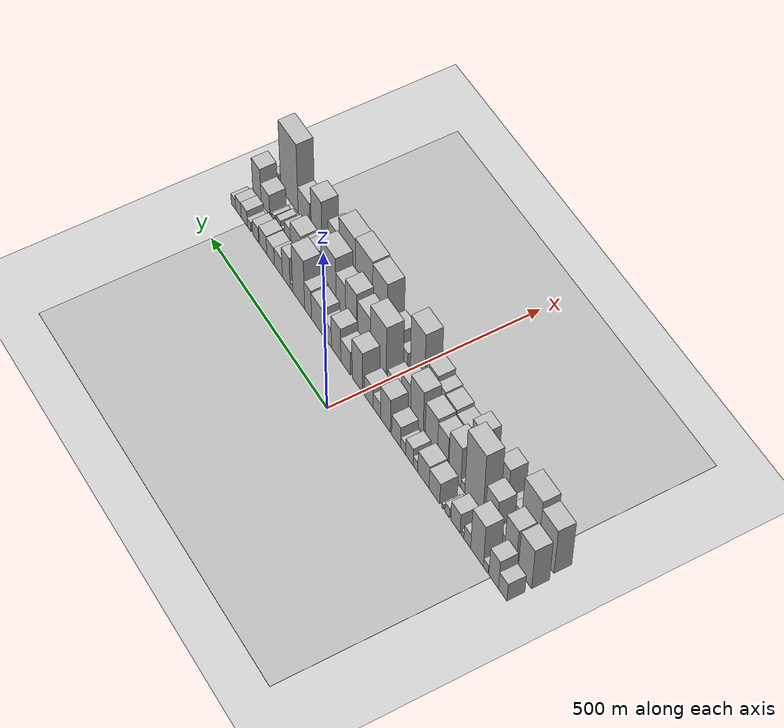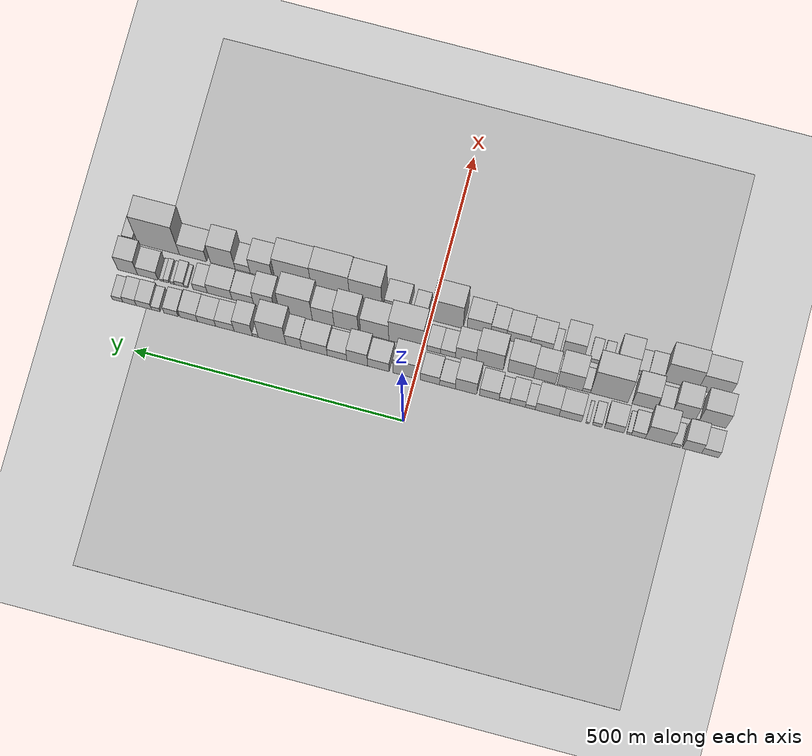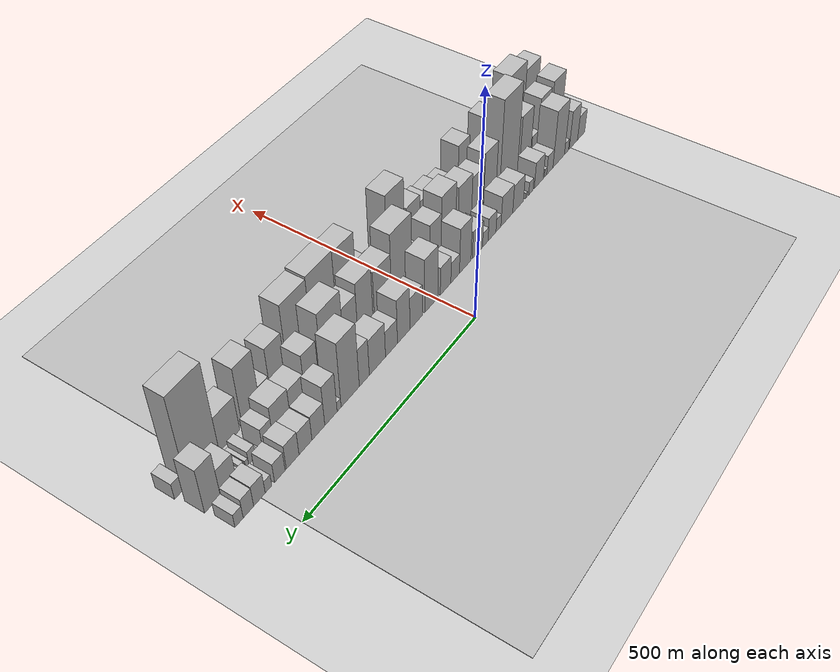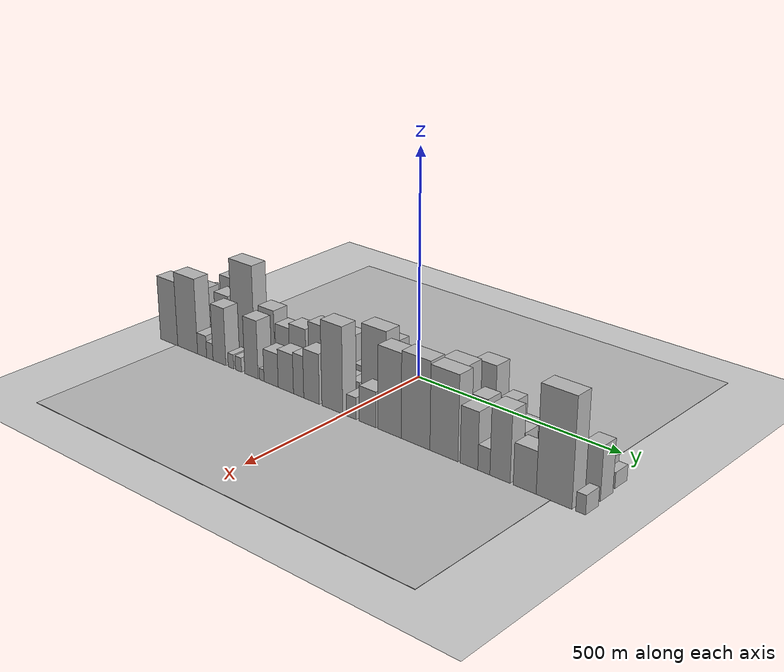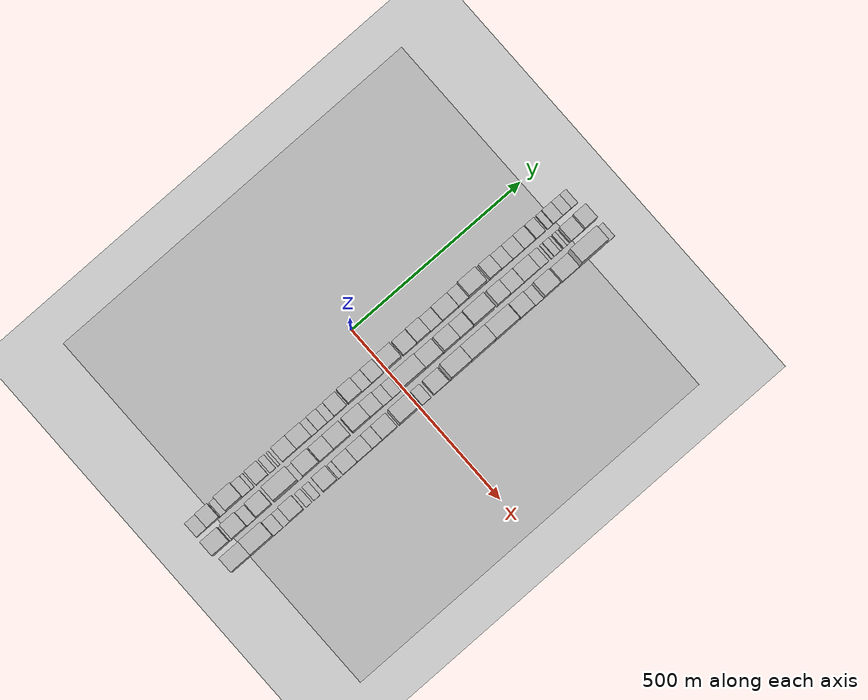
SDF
<?xml version="1.0" encoding="utf-8"?>

<sdf version="1.6">

   <world name="default">

      <gui fullscreen="0">

         <camera name="user_camera">

            <pose>-15 0 4.57585 0 0 0</pose>

            <view_controller>orbit</view_controller>

         </camera>

      </gui>

      <scene>

         <sky>

           <clouds>

             <speed>12</speed>

           </clouds>

         </sky>

         <ambient>0.4 0.4 0.4 1</ambient>

         <background>0.7 0.7 0.7 1</background>

         <shadows>1</shadows>

      </scene>

      <gravity>0 0 -9.8066</gravity>

      <magnetic_field>6e-06 2.3e-05 -4.2e-05</magnetic_field>

      <physics default="0" name="default_physics" type="ode">

         <ode>

            <solver>

               <type>quick</type>

               <iters>10</iters>

               <sor>1.0</sor>

               <use_dynamic_moi_rescaling>0</use_dynamic_moi_rescaling>

            </solver>

            <constraints>

               <cfm>0</cfm>

               <erp>0.2</erp>

               <contact_max_correcting_vel>100</contact_max_correcting_vel>

               <contact_surface_layer>0.001</contact_surface_layer>

            </constraints>

         </ode>

         <max_step_size>0.004</max_step_size>

         <real_time_factor>1</real_time_factor>

         <real_time_update_rate>250</real_time_update_rate>

      </physics>

      <light name="sun" type="directional">

         <cast_shadows>1</cast_shadows>

         <pose>0 0 10 0 0 0</pose>

         <diffuse>0.8 0.8 0.8 1</diffuse>

         <specular>0.2 0.2 0.2 1</specular>

         <attenuation>

            <range>1000</range>

            <constant>0.9</constant>

            <linear>0.01</linear>

            <quadratic>0.001</quadratic>

         </attenuation>

         <direction>-0.5 0.1 -0.9</direction>

      </light>

      <include>

         <name>ground_plane_1</name>

         <uri>model://HANNAS_ground_plane</uri>

         <pose>0 0 0  0 0 0</pose>

      </include>

      <include>

         <name>ground_plane_2</name>

         <uri>model://HANNAS_ground_plane</uri>

         <pose>100 0 0  0 0 0</pose>

      </include>

      <model name="building_1">

         <static>1</static>

         <pose frame="">100.0000 -544.3724 0 0.000000 0.000000 0.000000</pose>

         <link name="link">

            <pose frame="">0 0 30.00 0 0 0</pose>

            <collision name="collision">

               <geometry>

                  <box>

                     <size>40.0000 31.2552 60.0000</size>

                  </box>

               </geometry>

               <max_contacts>10</max_contacts>

               <surface>

                  <contact>

                     <ode/>

                  </contact>

                  <bounce/>

                  <friction>

                     <torsional>

                        <ode/>

                     </torsional>

                     <ode/>

                  </friction>

               </surface>

            </collision>

            <visual name="visual">

               <cast_shadows>0</cast_shadows>

               <geometry>

                  <box>

                     <size>40.0000 31.2552 60.0000</size>

                  </box>

               </geometry>

               <material>

                  <script>

                     <uri>model://HANNAS_wall/materials/scripts</uri>

                     <uri>model://HANNAS_wall/materials/textures</uri>

                     <name>vrc/HANNAS_wall</name>

                  </script>

               </material>

            </visual>

            <self_collide>0</self_collide>

            <enable_wind>0</enable_wind>

            <kinematic>0</kinematic>

         </link>

      </model>

      <model name="building_2">

         <static>1</static>

         <pose frame="">100.0000 -510.9200 0 0.000000 0.000000 0.000000</pose>

         <link name="link">

            <pose frame="">0 0 48.00 0 0 0</pose>

            <collision name="collision">

               <geometry>

                  <box>

                     <size>40.0000 35.6496 96.0000</size>

                  </box>

               </geometry>

               <max_contacts>10</max_contacts>

               <surface>

                  <contact>

                     <ode/>

                  </contact>

                  <bounce/>

                  <friction>

                     <torsional>

                        <ode/>

                     </torsional>

                     <ode/>

                  </friction>

               </surface>

            </collision>

            <visual name="visual">

               <cast_shadows>0</cast_shadows>

               <geometry>

                  <box>

                     <size>40.0000 35.6496 96.0000</size>

                  </box>

               </geometry>

               <material>

                  <script>

                     <uri>model://HANNAS_wall/materials/scripts</uri>

                     <uri>model://HANNAS_wall/materials/textures</uri>

                     <name>vrc/HANNAS_wall</name>

                  </script>

               </material>

            </visual>

            <self_collide>0</self_collide>

            <enable_wind>0</enable_wind>

            <kinematic>0</kinematic>

         </link>

      </model>

      <model name="building_3">

         <static>1</static>

         <pose frame="">100.0000 -481.4801 0 0.000000 0.000000 0.000000</pose>

         <link name="link">

            <pose frame="">0 0 15.00 0 0 0</pose>

            <collision name="collision">

               <geometry>

                  <box>

                     <size>40.0000 17.2301 30.0000</size>

                  </box>

               </geometry>

               <max_contacts>10</max_contacts>

               <surface>

                  <contact>

                     <ode/>

                  </contact>

                  <bounce/>

                  <friction>

                     <torsional>

                        <ode/>

                     </torsional>

                     <ode/>

                  </friction>

               </surface>

            </collision>

            <visual name="visual">

               <cast_shadows>0</cast_shadows>

               <geometry>

                  <box>

                     <size>40.0000 17.2301 30.0000</size>

                  </box>

               </geometry>

               <material>

                  <script>

                     <uri>model://HANNAS_wall/materials/scripts</uri>

                     <uri>model://HANNAS_wall/materials/textures</uri>

                     <name>vrc/HANNAS_wall</name>

                  </script>

               </material>

            </visual>

            <self_collide>0</self_collide>

            <enable_wind>0</enable_wind>

            <kinematic>0</kinematic>

         </link>

      </model>

      <model name="building_4">

         <static>1</static>

         <pose frame="">100.0000 -448.9706 0 0.000000 0.000000 0.000000</pose>

         <link name="link">

            <pose frame="">0 0 70.50 0 0 0</pose>

            <collision name="collision">

               <geometry>

                  <box>

                     <size>40.0000 47.7890 141.0000</size>

                  </box>

               </geometry>

               <max_contacts>10</max_contacts>

               <surface>

                  <contact>

                     <ode/>

                  </contact>

                  <bounce/>

                  <friction>

                     <torsional>

                        <ode/>

                     </torsional>

                     <ode/>

                  </friction>

               </surface>

            </collision>

            <visual name="visual">

               <cast_shadows>0</cast_shadows>

               <geometry>

                  <box>

                     <size>40.0000 47.7890 141.0000</size>

                  </box>

               </geometry>

               <material>

                  <script>

                     <uri>model://HANNAS_wall/materials/scripts</uri>

                     <uri>model://HANNAS_wall/materials/textures</uri>

                     <name>vrc/HANNAS_wall</name>

                  </script>

               </material>

            </visual>

            <self_collide>0</self_collide>

            <enable_wind>0</enable_wind>

            <kinematic>0</kinematic>

         </link>

      </model>

      <model name="building_5">

         <static>1</static>

         <pose frame="">100.0000 -412.3479 0 0.000000 0.000000 0.000000</pose>

         <link name="link">

            <pose frame="">0 0 24.00 0 0 0</pose>

            <collision name="collision">

               <geometry>

                  <box>

                     <size>40.0000 25.4565 48.0000</size>

                  </box>

               </geometry>

               <max_contacts>10</max_contacts>

               <surface>

                  <contact>

                     <ode/>

                  </contact>

                  <bounce/>

                  <friction>

                     <torsional>

                        <ode/>

                     </torsional>

                     <ode/>

                  </friction>

               </surface>

            </collision>

            <visual name="visual">

               <cast_shadows>0</cast_shadows>

               <geometry>

                  <box>

                     <size>40.0000 25.4565 48.0000</size>

                  </box>

               </geometry>

               <material>

                  <script>

                     <uri>model://HANNAS_wall/materials/scripts</uri>

                     <uri>model://HANNAS_wall/materials/textures</uri>

                     <name>vrc/HANNAS_wall</name>

                  </script>

               </material>

            </visual>

            <self_collide>0</self_collide>

            <enable_wind>0</enable_wind>

            <kinematic>0</kinematic>

         </link>

      </model>

      <model name="building_6">

         <static>1</static>

         <pose frame="">100.0000 -395.1391 0 0.000000 0.000000 0.000000</pose>

         <link name="link">

            <pose frame="">0 0 10.50 0 0 0</pose>

            <collision name="collision">

               <geometry>

                  <box>

                     <size>40.0000 8.9609 21.0000</size>

                  </box>

               </geometry>

               <max_contacts>10</max_contacts>

               <surface>

                  <contact>

                     <ode/>

                  </contact>

                  <bounce/>

                  <friction>

                     <torsional>

                        <ode/>

                     </torsional>

                     <ode/>

                  </friction>

               </surface>

            </collision>

            <visual name="visual">

               <cast_shadows>0</cast_shadows>

               <geometry>

                  <box>

                     <size>40.0000 8.9609 21.0000</size>

                  </box>

               </geometry>

               <material>

                  <script>

                     <uri>model://HANNAS_wall/materials/scripts</uri>

                     <uri>model://HANNAS_wall/materials/textures</uri>

                     <name>vrc/HANNAS_wall</name>

                  </script>

               </material>

            </visual>

            <self_collide>0</self_collide>

            <enable_wind>0</enable_wind>

            <kinematic>0</kinematic>

         </link>

      </model>

      <model name="building_7">

         <static>1</static>

         <pose frame="">100.0000 -367.8494 0 0.000000 0.000000 0.000000</pose>

         <link name="link">

            <pose frame="">0 0 33.00 0 0 0</pose>

            <collision name="collision">

               <geometry>

                  <box>

                     <size>40.0000 35.6186 66.0000</size>

                  </box>

               </geometry>

               <max_contacts>10</max_contacts>

               <surface>

                  <contact>

                     <ode/>

                  </contact>

                  <bounce/>

                  <friction>

                     <torsional>

                        <ode/>

                     </torsional>

                     <ode/>

                  </friction>

               </surface>

            </collision>

            <visual name="visual">

               <cast_shadows>0</cast_shadows>

               <geometry>

                  <box>

                     <size>40.0000 35.6186 66.0000</size>

                  </box>

               </geometry>

               <material>

                  <script>

                     <uri>model://HANNAS_wall/materials/scripts</uri>

                     <uri>model://HANNAS_wall/materials/textures</uri>

                     <name>vrc/HANNAS_wall</name>

                  </script>

               </material>

            </visual>

            <self_collide>0</self_collide>

            <enable_wind>0</enable_wind>

            <kinematic>0</kinematic>

         </link>

      </model>

      <model name="building_8">

         <static>1</static>

         <pose frame="">100.0000 -336.5735 0 0.000000 0.000000 0.000000</pose>

         <link name="link">

            <pose frame="">0 0 16.50 0 0 0</pose>

            <collision name="collision">

               <geometry>

                  <box>

                     <size>40.0000 16.9333 33.0000</size>

                  </box>

               </geometry>

               <max_contacts>10</max_contacts>

               <surface>

                  <contact>

                     <ode/>

                  </contact>

                  <bounce/>

                  <friction>

                     <torsional>

                        <ode/>

                     </torsional>

                     <ode/>

                  </friction>

               </surface>

            </collision>

            <visual name="visual">

               <cast_shadows>0</cast_shadows>

               <geometry>

                  <box>

                     <size>40.0000 16.9333 33.0000</size>

                  </box>

               </geometry>

               <material>

                  <script>

                     <uri>model://HANNAS_wall/materials/scripts</uri>

                     <uri>model://HANNAS_wall/materials/textures</uri>

                     <name>vrc/HANNAS_wall</name>

                  </script>

               </material>

            </visual>

            <self_collide>0</self_collide>

            <enable_wind>0</enable_wind>

            <kinematic>0</kinematic>

         </link>

      </model>

      <model name="building_9">

         <static>1</static>

         <pose frame="">100.0000 -318.8743 0 0.000000 0.000000 0.000000</pose>

         <link name="link">

            <pose frame="">0 0 7.50 0 0 0</pose>

            <collision name="collision">

               <geometry>

                  <box>

                     <size>40.0000 6.4653 15.0000</size>

                  </box>

               </geometry>

               <max_contacts>10</max_contacts>

               <surface>

                  <contact>

                     <ode/>

                  </contact>

                  <bounce/>

                  <friction>

                     <torsional>

                        <ode/>

                     </torsional>

                     <ode/>

                  </friction>

               </surface>

            </collision>

            <visual name="visual">

               <cast_shadows>0</cast_shadows>

               <geometry>

                  <box>

                     <size>40.0000 6.4653 15.0000</size>

                  </box>

               </geometry>

               <material>

                  <script>

                     <uri>model://HANNAS_wall/materials/scripts</uri>

                     <uri>model://HANNAS_wall/materials/textures</uri>

                     <name>vrc/HANNAS_wall</name>

                  </script>

               </material>

            </visual>

            <self_collide>0</self_collide>

            <enable_wind>0</enable_wind>

            <kinematic>0</kinematic>

         </link>

      </model>

      <model name="building_10">

         <static>1</static>

         <pose frame="">100.0000 -286.9913 0 0.000000 0.000000 0.000000</pose>

         <link name="link">

            <pose frame="">0 0 34.50 0 0 0</pose>

            <collision name="collision">

               <geometry>

                  <box>

                     <size>40.0000 41.3007 69.0000</size>

                  </box>

               </geometry>

               <max_contacts>10</max_contacts>

               <surface>

                  <contact>

                     <ode/>

                  </contact>

                  <bounce/>

                  <friction>

                     <torsional>

                        <ode/>

                     </torsional>

                     <ode/>

                  </friction>

               </surface>

            </collision>

            <visual name="visual">

               <cast_shadows>0</cast_shadows>

               <geometry>

                  <box>

                     <size>40.0000 41.3007 69.0000</size>

                  </box>

               </geometry>

               <material>

                  <script>

                     <uri>model://HANNAS_wall/materials/scripts</uri>

                     <uri>model://HANNAS_wall/materials/textures</uri>

                     <name>vrc/HANNAS_wall</name>

                  </script>

               </material>

            </visual>

            <self_collide>0</self_collide>

            <enable_wind>0</enable_wind>

            <kinematic>0</kinematic>

         </link>

      </model>

      <model name="building_11">

         <static>1</static>

         <pose frame="">100.0000 -244.3945 0 0.000000 0.000000 0.000000</pose>

         <link name="link">

            <pose frame="">0 0 37.50 0 0 0</pose>

            <collision name="collision">

               <geometry>

                  <box>

                     <size>40.0000 43.8927 75.0000</size>

                  </box>

               </geometry>

               <max_contacts>10</max_contacts>

               <surface>

                  <contact>

                     <ode/>

                  </contact>

                  <bounce/>

                  <friction>

                     <torsional>

                        <ode/>

                     </torsional>

                     <ode/>

                  </friction>

               </surface>

            </collision>

            <visual name="visual">

               <cast_shadows>0</cast_shadows>

               <geometry>

                  <box>

                     <size>40.0000 43.8927 75.0000</size>

                  </box>

               </geometry>

               <material>

                  <script>

                     <uri>model://HANNAS_wall/materials/scripts</uri>

                     <uri>model://HANNAS_wall/materials/textures</uri>

                     <name>vrc/HANNAS_wall</name>

                  </script>

               </material>

            </visual>

            <self_collide>0</self_collide>

            <enable_wind>0</enable_wind>

            <kinematic>0</kinematic>

         </link>

      </model>

      <model name="building_12">

         <static>1</static>

         <pose frame="">100.0000 -213.2445 0 0.000000 0.000000 0.000000</pose>

         <link name="link">

            <pose frame="">0 0 16.50 0 0 0</pose>

            <collision name="collision">

               <geometry>

                  <box>

                     <size>40.0000 18.4073 33.0000</size>

                  </box>

               </geometry>

               <max_contacts>10</max_contacts>

               <surface>

                  <contact>

                     <ode/>

                  </contact>

                  <bounce/>

                  <friction>

                     <torsional>

                        <ode/>

                     </torsional>

                     <ode/>

                  </friction>

               </surface>

            </collision>

            <visual name="visual">

               <cast_shadows>0</cast_shadows>

               <geometry>

                  <box>

                     <size>40.0000 18.4073 33.0000</size>

                  </box>

               </geometry>

               <material>

                  <script>

                     <uri>model://HANNAS_wall/materials/scripts</uri>

                     <uri>model://HANNAS_wall/materials/textures</uri>

                     <name>vrc/HANNAS_wall</name>

                  </script>

               </material>

            </visual>

            <self_collide>0</self_collide>

            <enable_wind>0</enable_wind>

            <kinematic>0</kinematic>

         </link>

      </model>

      <model name="building_13">

         <static>1</static>

         <pose frame="">100.0000 -189.7287 0 0.000000 0.000000 0.000000</pose>

         <link name="link">

            <pose frame="">0 0 28.50 0 0 0</pose>

            <collision name="collision">

               <geometry>

                  <box>

                     <size>40.0000 28.6245 57.0000</size>

                  </box>

               </geometry>

               <max_contacts>10</max_contacts>

               <surface>

                  <contact>

                     <ode/>

                  </contact>

                  <bounce/>

                  <friction>

                     <torsional>

                        <ode/>

                     </torsional>

                     <ode/>

                  </friction>

               </surface>

            </collision>

            <visual name="visual">

               <cast_shadows>0</cast_shadows>

               <geometry>

                  <box>

                     <size>40.0000 28.6245 57.0000</size>

                  </box>

               </geometry>

               <material>

                  <script>

                     <uri>model://HANNAS_wall/materials/scripts</uri>

                     <uri>model://HANNAS_wall/materials/textures</uri>

                     <name>vrc/HANNAS_wall</name>

                  </script>

               </material>

            </visual>

            <self_collide>0</self_collide>

            <enable_wind>0</enable_wind>

            <kinematic>0</kinematic>

         </link>

      </model>

      <model name="building_14">

         <static>1</static>

         <pose frame="">100.0000 -165.3900 0 0.000000 0.000000 0.000000</pose>

         <link name="link">

            <pose frame="">0 0 18.00 0 0 0</pose>

            <collision name="collision">

               <geometry>

                  <box>

                     <size>40.0000 20.0529 36.0000</size>

                  </box>

               </geometry>

               <max_contacts>10</max_contacts>

               <surface>

                  <contact>

                     <ode/>

                  </contact>

                  <bounce/>

                  <friction>

                     <torsional>

                        <ode/>

                     </torsional>

                     <ode/>

                  </friction>

               </surface>

            </collision>

            <visual name="visual">

               <cast_shadows>0</cast_shadows>

               <geometry>

                  <box>

                     <size>40.0000 20.0529 36.0000</size>

                  </box>

               </geometry>

               <material>

                  <script>

                     <uri>model://HANNAS_wall/materials/scripts</uri>

                     <uri>model://HANNAS_wall/materials/textures</uri>

                     <name>vrc/HANNAS_wall</name>

                  </script>

               </material>

            </visual>

            <self_collide>0</self_collide>

            <enable_wind>0</enable_wind>

            <kinematic>0</kinematic>

         </link>

      </model>

      <model name="building_15">

         <static>1</static>

         <pose frame="">100.0000 -137.2105 0 0.000000 0.000000 0.000000</pose>

         <link name="link">

            <pose frame="">0 0 34.50 0 0 0</pose>

            <collision name="collision">

               <geometry>

                  <box>

                     <size>40.0000 36.3060 69.0000</size>

                  </box>

               </geometry>

               <max_contacts>10</max_contacts>

               <surface>

                  <contact>

                     <ode/>

                  </contact>

                  <bounce/>

                  <friction>

                     <torsional>

                        <ode/>

                     </torsional>

                     <ode/>

                  </friction>

               </surface>

            </collision>

            <visual name="visual">

               <cast_shadows>0</cast_shadows>

               <geometry>

                  <box>

                     <size>40.0000 36.3060 69.0000</size>

                  </box>

               </geometry>

               <material>

                  <script>

                     <uri>model://HANNAS_wall/materials/scripts</uri>

                     <uri>model://HANNAS_wall/materials/textures</uri>

                     <name>vrc/HANNAS_wall</name>

                  </script>

               </material>

            </visual>

            <self_collide>0</self_collide>

            <enable_wind>0</enable_wind>

            <kinematic>0</kinematic>

         </link>

      </model>

      <model name="building_16">

         <static>1</static>

         <pose frame="">100.0000 -94.3048 0 0.000000 0.000000 0.000000</pose>

         <link name="link">

            <pose frame="">0 0 55.50 0 0 0</pose>

            <collision name="collision">

               <geometry>

                  <box>

                     <size>40.0000 39.5055 111.0000</size>

                  </box>

               </geometry>

               <max_contacts>10</max_contacts>

               <surface>

                  <contact>

                     <ode/>

                  </contact>

                  <bounce/>

                  <friction>

                     <torsional>

                        <ode/>

                     </torsional>

                     <ode/>

                  </friction>

               </surface>

            </collision>

            <visual name="visual">

               <cast_shadows>0</cast_shadows>

               <geometry>

                  <box>

                     <size>40.0000 39.5055 111.0000</size>

                  </box>

               </geometry>

               <material>

                  <script>

                     <uri>model://HANNAS_wall/materials/scripts</uri>

                     <uri>model://HANNAS_wall/materials/textures</uri>

                     <name>vrc/HANNAS_wall</name>

                  </script>

               </material>

            </visual>

            <self_collide>0</self_collide>

            <enable_wind>0</enable_wind>

            <kinematic>0</kinematic>

         </link>

      </model>

      <model name="building_17">

         <static>1</static>

         <pose frame="">100.0000 -59.9479 0 0.000000 0.000000 0.000000</pose>

         <link name="link">

            <pose frame="">0 0 25.50 0 0 0</pose>

            <collision name="collision">

               <geometry>

                  <box>

                     <size>40.0000 29.2083 51.0000</size>

                  </box>

               </geometry>

               <max_contacts>10</max_contacts>

               <surface>

                  <contact>

                     <ode/>

                  </contact>

                  <bounce/>

                  <friction>

                     <torsional>

                        <ode/>

                     </torsional>

                     <ode/>

                  </friction>

               </surface>

            </collision>

            <visual name="visual">

               <cast_shadows>0</cast_shadows>

               <geometry>

                  <box>

                     <size>40.0000 29.2083 51.0000</size>

                  </box>

               </geometry>

               <material>

                  <script>

                     <uri>model://HANNAS_wall/materials/scripts</uri>

                     <uri>model://HANNAS_wall/materials/textures</uri>

                     <name>vrc/HANNAS_wall</name>

                  </script>

               </material>

            </visual>

            <self_collide>0</self_collide>

            <enable_wind>0</enable_wind>

            <kinematic>0</kinematic>

         </link>

      </model>

      <model name="building_18">

         <static>1</static>

         <pose frame="">100.0000 -27.5950 0 0.000000 0.000000 0.000000</pose>

         <link name="link">

            <pose frame="">0 0 34.50 0 0 0</pose>

            <collision name="collision">

               <geometry>

                  <box>

                     <size>40.0000 35.4975 69.0000</size>

                  </box>

               </geometry>

               <max_contacts>10</max_contacts>

               <surface>

                  <contact>

                     <ode/>

                  </contact>

                  <bounce/>

                  <friction>

                     <torsional>

                        <ode/>

                     </torsional>

                     <ode/>

                  </friction>

               </surface>

            </collision>

            <visual name="visual">

               <cast_shadows>0</cast_shadows>

               <geometry>

                  <box>

                     <size>40.0000 35.4975 69.0000</size>

                  </box>

               </geometry>

               <material>

                  <script>

                     <uri>model://HANNAS_wall/materials/scripts</uri>

                     <uri>model://HANNAS_wall/materials/textures</uri>

                     <name>vrc/HANNAS_wall</name>

                  </script>

               </material>

            </visual>

            <self_collide>0</self_collide>

            <enable_wind>0</enable_wind>

            <kinematic>0</kinematic>

         </link>

      </model>

      <model name="building_19">

         <static>1</static>

         <pose frame="">100.0000 19.4768 0 0.000000 0.000000 0.000000</pose>

         <link name="link">

            <pose frame="">0 0 66.00 0 0 0</pose>

            <collision name="collision">

               <geometry>

                  <box>

                     <size>40.0000 42.6460 132.0000</size>

                  </box>

               </geometry>

               <max_contacts>10</max_contacts>

               <surface>

                  <contact>

                     <ode/>

                  </contact>

                  <bounce/>

                  <friction>

                     <torsional>

                        <ode/>

                     </torsional>

                     <ode/>

                  </friction>

               </surface>

            </collision>

            <visual name="visual">

               <cast_shadows>0</cast_shadows>

               <geometry>

                  <box>

                     <size>40.0000 42.6460 132.0000</size>

                  </box>

               </geometry>

               <material>

                  <script>

                     <uri>model://HANNAS_wall/materials/scripts</uri>

                     <uri>model://HANNAS_wall/materials/textures</uri>

                     <name>vrc/HANNAS_wall</name>

                  </script>

               </material>

            </visual>

            <self_collide>0</self_collide>

            <enable_wind>0</enable_wind>

            <kinematic>0</kinematic>

         </link>

      </model>

      <model name="building_20">

         <static>1</static>

         <pose frame="">100.0000 67.7031 0 0.000000 0.000000 0.000000</pose>

         <link name="link">

            <pose frame="">0 0 39.00 0 0 0</pose>

            <collision name="collision">

               <geometry>

                  <box>

                     <size>40.0000 39.8066 78.0000</size>

                  </box>

               </geometry>

               <max_contacts>10</max_contacts>

               <surface>

                  <contact>

                     <ode/>

                  </contact>

                  <bounce/>

                  <friction>

                     <torsional>

                        <ode/>

                     </torsional>

                     <ode/>

                  </friction>

               </surface>

            </collision>

            <visual name="visual">

               <cast_shadows>0</cast_shadows>

               <geometry>

                  <box>

                     <size>40.0000 39.8066 78.0000</size>

                  </box>

               </geometry>

               <material>

                  <script>

                     <uri>model://HANNAS_wall/materials/scripts</uri>

                     <uri>model://HANNAS_wall/materials/textures</uri>

                     <name>vrc/HANNAS_wall</name>

                  </script>

               </material>

            </visual>

            <self_collide>0</self_collide>

            <enable_wind>0</enable_wind>

            <kinematic>0</kinematic>

         </link>

      </model>

      <model name="building_21">

         <static>1</static>

         <pose frame="">100.0000 107.0174 0 0.000000 0.000000 0.000000</pose>

         <link name="link">

            <pose frame="">0 0 54.00 0 0 0</pose>

            <collision name="collision">

               <geometry>

                  <box>

                     <size>40.0000 38.8219 108.0000</size>

                  </box>

               </geometry>

               <max_contacts>10</max_contacts>

               <surface>

                  <contact>

                     <ode/>

                  </contact>

                  <bounce/>

                  <friction>

                     <torsional>

                        <ode/>

                     </torsional>

                     <ode/>

                  </friction>

               </surface>

            </collision>

            <visual name="visual">

               <cast_shadows>0</cast_shadows>

               <geometry>

                  <box>

                     <size>40.0000 38.8219 108.0000</size>

                  </box>

               </geometry>

               <material>

                  <script>

                     <uri>model://HANNAS_wall/materials/scripts</uri>

                     <uri>model://HANNAS_wall/materials/textures</uri>

                     <name>vrc/HANNAS_wall</name>

                  </script>

               </material>

            </visual>

            <self_collide>0</self_collide>

            <enable_wind>0</enable_wind>

            <kinematic>0</kinematic>

         </link>

      </model>

      <model name="building_22">

         <static>1</static>

         <pose frame="">100.0000 144.5804 0 0.000000 0.000000 0.000000</pose>

         <link name="link">

            <pose frame="">0 0 31.50 0 0 0</pose>

            <collision name="collision">

               <geometry>

                  <box>

                     <size>40.0000 36.3041 63.0000</size>

                  </box>

               </geometry>

               <max_contacts>10</max_contacts>

               <surface>

                  <contact>

                     <ode/>

                  </contact>

                  <bounce/>

                  <friction>

                     <torsional>

                        <ode/>

                     </torsional>

                     <ode/>

                  </friction>

               </surface>

            </collision>

            <visual name="visual">

               <cast_shadows>0</cast_shadows>

               <geometry>

                  <box>

                     <size>40.0000 36.3041 63.0000</size>

                  </box>

               </geometry>

               <material>

                  <script>

                     <uri>model://HANNAS_wall/materials/scripts</uri>

                     <uri>model://HANNAS_wall/materials/textures</uri>

                     <name>vrc/HANNAS_wall</name>

                  </script>

               </material>

            </visual>

            <self_collide>0</self_collide>

            <enable_wind>0</enable_wind>

            <kinematic>0</kinematic>

         </link>

      </model>

      <model name="building_23">

         <static>1</static>

         <pose frame="">100.0000 186.6478 0 0.000000 0.000000 0.000000</pose>

         <link name="link">

            <pose frame="">0 0 43.50 0 0 0</pose>

            <collision name="collision">

               <geometry>

                  <box>

                     <size>40.0000 47.8308 87.0000</size>

                  </box>

               </geometry>

               <max_contacts>10</max_contacts>

               <surface>

                  <contact>

                     <ode/>

                  </contact>

                  <bounce/>

                  <friction>

                     <torsional>

                        <ode/>

                     </torsional>

                     <ode/>

                  </friction>

               </surface>

            </collision>

            <visual name="visual">

               <cast_shadows>0</cast_shadows>

               <geometry>

                  <box>

                     <size>40.0000 47.8308 87.0000</size>

                  </box>

               </geometry>

               <material>

                  <script>

                     <uri>model://HANNAS_wall/materials/scripts</uri>

                     <uri>model://HANNAS_wall/materials/textures</uri>

                     <name>vrc/HANNAS_wall</name>

                  </script>

               </material>

            </visual>

            <self_collide>0</self_collide>

            <enable_wind>0</enable_wind>

            <kinematic>0</kinematic>

         </link>

      </model>

      <model name="building_24">

         <static>1</static>

         <pose frame="">100.0000 225.0779 0 0.000000 0.000000 0.000000</pose>

         <link name="link">

            <pose frame="">0 0 46.50 0 0 0</pose>

            <collision name="collision">

               <geometry>

                  <box>

                     <size>40.0000 29.0294 93.0000</size>

                  </box>

               </geometry>

               <max_contacts>10</max_contacts>

               <surface>

                  <contact>

                     <ode/>

                  </contact>

                  <bounce/>

                  <friction>

                     <torsional>

                        <ode/>

                     </torsional>

                     <ode/>

                  </friction>

               </surface>

            </collision>

            <visual name="visual">

               <cast_shadows>0</cast_shadows>

               <geometry>

                  <box>

                     <size>40.0000 29.0294 93.0000</size>

                  </box>

               </geometry>

               <material>

                  <script>

                     <uri>model://HANNAS_wall/materials/scripts</uri>

                     <uri>model://HANNAS_wall/materials/textures</uri>

                     <name>vrc/HANNAS_wall</name>

                  </script>

               </material>

            </visual>

            <self_collide>0</self_collide>

            <enable_wind>0</enable_wind>

            <kinematic>0</kinematic>

         </link>

      </model>

      <model name="building_25">

         <static>1</static>

         <pose frame="">100.0000 265.3183 0 0.000000 0.000000 0.000000</pose>

         <link name="link">

            <pose frame="">0 0 79.50 0 0 0</pose>

            <collision name="collision">

               <geometry>

                  <box>

                     <size>40.0000 51.4513 159.0000</size>

                  </box>

               </geometry>

               <max_contacts>10</max_contacts>

               <surface>

                  <contact>

                     <ode/>

                  </contact>

                  <bounce/>

                  <friction>

                     <torsional>

                        <ode/>

                     </torsional>

                     <ode/>

                  </friction>

               </surface>

            </collision>

            <visual name="visual">

               <cast_shadows>0</cast_shadows>

               <geometry>

                  <box>

                     <size>40.0000 51.4513 159.0000</size>

                  </box>

               </geometry>

               <material>

                  <script>

                     <uri>model://HANNAS_wall/materials/scripts</uri>

                     <uri>model://HANNAS_wall/materials/textures</uri>

                     <name>vrc/HANNAS_wall</name>

                  </script>

               </material>

            </visual>

            <self_collide>0</self_collide>

            <enable_wind>0</enable_wind>

            <kinematic>0</kinematic>

         </link>

      </model>

      <model name="building_26">

         <static>1</static>

         <pose frame="">100.0000 296.5608 0 0.000000 0.000000 0.000000</pose>

         <link name="link">

            <pose frame="">0 0 12.00 0 0 0</pose>

            <collision name="collision">

               <geometry>

                  <box>

                     <size>40.0000 11.0336 24.0000</size>

                  </box>

               </geometry>

               <max_contacts>10</max_contacts>

               <surface>

                  <contact>

                     <ode/>

                  </contact>

                  <bounce/>

                  <friction>

                     <torsional>

                        <ode/>

                     </torsional>

                     <ode/>

                  </friction>

               </surface>

            </collision>

            <visual name="visual">

               <cast_shadows>0</cast_shadows>

               <geometry>

                  <box>

                     <size>40.0000 11.0336 24.0000</size>

                  </box>

               </geometry>

               <material>

                  <script>

                     <uri>model://HANNAS_wall/materials/scripts</uri>

                     <uri>model://HANNAS_wall/materials/textures</uri>

                     <name>vrc/HANNAS_wall</name>

                  </script>

               </material>

            </visual>

            <self_collide>0</self_collide>

            <enable_wind>0</enable_wind>

            <kinematic>0</kinematic>

         </link>

      </model>

      <model name="building_27">

         <static>1</static>

         <pose frame="">100.0000 318.9848 0 0.000000 0.000000 0.000000</pose>

         <link name="link">

            <pose frame="">0 0 49.50 0 0 0</pose>

            <collision name="collision">

               <geometry>

                  <box>

                     <size>40.0000 33.8144 99.0000</size>

                  </box>

               </geometry>

               <max_contacts>10</max_contacts>

               <surface>

                  <contact>

                     <ode/>

                  </contact>

                  <bounce/>

                  <friction>

                     <torsional>

                        <ode/>

                     </torsional>

                     <ode/>

                  </friction>

               </surface>

            </collision>

            <visual name="visual">

               <cast_shadows>0</cast_shadows>

               <geometry>

                  <box>

                     <size>40.0000 33.8144 99.0000</size>

                  </box>

               </geometry>

               <material>

                  <script>

                     <uri>model://HANNAS_wall/materials/scripts</uri>

                     <uri>model://HANNAS_wall/materials/textures</uri>

                     <name>vrc/HANNAS_wall</name>

                  </script>

               </material>

            </visual>

            <self_collide>0</self_collide>

            <enable_wind>0</enable_wind>

            <kinematic>0</kinematic>

         </link>

      </model>

      <model name="building_28">

         <static>1</static>

         <pose frame="">100.0000 353.1228 0 0.000000 0.000000 0.000000</pose>

         <link name="link">

            <pose frame="">0 0 30.00 0 0 0</pose>

            <collision name="collision">

               <geometry>

                  <box>

                     <size>40.0000 34.4616 60.0000</size>

                  </box>

               </geometry>

               <max_contacts>10</max_contacts>

               <surface>

                  <contact>

                     <ode/>

                  </contact>

                  <bounce/>

                  <friction>

                     <torsional>

                        <ode/>

                     </torsional>

                     <ode/>

                  </friction>

               </surface>

            </collision>

            <visual name="visual">

               <cast_shadows>0</cast_shadows>

               <geometry>

                  <box>

                     <size>40.0000 34.4616 60.0000</size>

                  </box>

               </geometry>

               <material>

                  <script>

                     <uri>model://HANNAS_wall/materials/scripts</uri>

                     <uri>model://HANNAS_wall/materials/textures</uri>

                     <name>vrc/HANNAS_wall</name>

                  </script>

               </material>

            </visual>

            <self_collide>0</self_collide>

            <enable_wind>0</enable_wind>

            <kinematic>0</kinematic>

         </link>

      </model>

      <model name="building_29">

         <static>1</static>

         <pose frame="">100.0000 387.3583 0 0.000000 0.000000 0.000000</pose>

         <link name="link">

            <pose frame="">0 0 28.50 0 0 0</pose>

            <collision name="collision">

               <geometry>

                  <box>

                     <size>40.0000 34.0094 57.0000</size>

                  </box>

               </geometry>

               <max_contacts>10</max_contacts>

               <surface>

                  <contact>

                     <ode/>

                  </contact>

                  <bounce/>

                  <friction>

                     <torsional>

                        <ode/>

                     </torsional>

                     <ode/>

                  </friction>

               </surface>

            </collision>

            <visual name="visual">

               <cast_shadows>0</cast_shadows>

               <geometry>

                  <box>

                     <size>40.0000 34.0094 57.0000</size>

                  </box>

               </geometry>

               <material>

                  <script>

                     <uri>model://HANNAS_wall/materials/scripts</uri>

                     <uri>model://HANNAS_wall/materials/textures</uri>

                     <name>vrc/HANNAS_wall</name>

                  </script>

               </material>

            </visual>

            <self_collide>0</self_collide>

            <enable_wind>0</enable_wind>

            <kinematic>0</kinematic>

         </link>

      </model>

      <model name="building_30">

         <static>1</static>

         <pose frame="">100.0000 420.7903 0 0.000000 0.000000 0.000000</pose>

         <link name="link">

            <pose frame="">0 0 30.00 0 0 0</pose>

            <collision name="collision">

               <geometry>

                  <box>

                     <size>40.0000 32.8547 60.0000</size>

                  </box>

               </geometry>

               <max_contacts>10</max_contacts>

               <surface>

                  <contact>

                     <ode/>

                  </contact>

                  <bounce/>

                  <friction>

                     <torsional>

                        <ode/>

                     </torsional>

                     <ode/>

                  </friction>

               </surface>

            </collision>

            <visual name="visual">

               <cast_shadows>0</cast_shadows>

               <geometry>

                  <box>

                     <size>40.0000 32.8547 60.0000</size>

                  </box>

               </geometry>

               <material>

                  <script>

                     <uri>model://HANNAS_wall/materials/scripts</uri>

                     <uri>model://HANNAS_wall/materials/textures</uri>

                     <name>vrc/HANNAS_wall</name>

                  </script>

               </material>

            </visual>

            <self_collide>0</self_collide>

            <enable_wind>0</enable_wind>

            <kinematic>0</kinematic>

         </link>

      </model>

      <model name="building_31">

         <static>1</static>

         <pose frame="">100.0000 453.5304 0 0.000000 0.000000 0.000000</pose>

         <link name="link">

            <pose frame="">0 0 24.00 0 0 0</pose>

            <collision name="collision">

               <geometry>

                  <box>

                     <size>40.0000 26.6255 48.0000</size>

                  </box>

               </geometry>

               <max_contacts>10</max_contacts>

               <surface>

                  <contact>

                     <ode/>

                  </contact>

                  <bounce/>

                  <friction>

                     <torsional>

                        <ode/>

                     </torsional>

                     <ode/>

                  </friction>

               </surface>

            </collision>

            <visual name="visual">

               <cast_shadows>0</cast_shadows>

               <geometry>

                  <box>

                     <size>40.0000 26.6255 48.0000</size>

                  </box>

               </geometry>

               <material>

                  <script>

                     <uri>model://HANNAS_wall/materials/scripts</uri>

                     <uri>model://HANNAS_wall/materials/textures</uri>

                     <name>vrc/HANNAS_wall</name>

                  </script>

               </material>

            </visual>

            <self_collide>0</self_collide>

            <enable_wind>0</enable_wind>

            <kinematic>0</kinematic>

         </link>

      </model>

      <model name="building_32">

         <static>1</static>

         <pose frame="">100.0000 481.9399 0 0.000000 0.000000 0.000000</pose>

         <link name="link">

            <pose frame="">0 0 15.00 0 0 0</pose>

            <collision name="collision">

               <geometry>

                  <box>

                     <size>40.0000 16.1936 30.0000</size>

                  </box>

               </geometry>

               <max_contacts>10</max_contacts>

               <surface>

                  <contact>

                     <ode/>

                  </contact>

                  <bounce/>

                  <friction>

                     <torsional>

                        <ode/>

                     </torsional>

                     <ode/>

                  </friction>

               </surface>

            </collision>

            <visual name="visual">

               <cast_shadows>0</cast_shadows>

               <geometry>

                  <box>

                     <size>40.0000 16.1936 30.0000</size>

                  </box>

               </geometry>

               <material>

                  <script>

                     <uri>model://HANNAS_wall/materials/scripts</uri>

                     <uri>model://HANNAS_wall/materials/textures</uri>

                     <name>vrc/HANNAS_wall</name>

                  </script>

               </material>

            </visual>

            <self_collide>0</self_collide>

            <enable_wind>0</enable_wind>

            <kinematic>0</kinematic>

         </link>

      </model>

      <model name="building_33">

         <static>1</static>

         <pose frame="">100.0000 504.1276 0 0.000000 0.000000 0.000000</pose>

         <link name="link">

            <pose frame="">0 0 25.50 0 0 0</pose>

            <collision name="collision">

               <geometry>

                  <box>

                     <size>40.0000 28.1818 51.0000</size>

                  </box>

               </geometry>

               <max_contacts>10</max_contacts>

               <surface>

                  <contact>

                     <ode/>

                  </contact>

                  <bounce/>

                  <friction>

                     <torsional>

                        <ode/>

                     </torsional>

                     <ode/>

                  </friction>

               </surface>

            </collision>

            <visual name="visual">

               <cast_shadows>0</cast_shadows>

               <geometry>

                  <box>

                     <size>40.0000 28.1818 51.0000</size>

                  </box>

               </geometry>

               <material>

                  <script>

                     <uri>model://HANNAS_wall/materials/scripts</uri>

                     <uri>model://HANNAS_wall/materials/textures</uri>

                     <name>vrc/HANNAS_wall</name>

                  </script>

               </material>

            </visual>

            <self_collide>0</self_collide>

            <enable_wind>0</enable_wind>

            <kinematic>0</kinematic>

         </link>

      </model>

      <model name="building_34">

         <static>1</static>

         <pose frame="">100.0000 530.7570 0 0.000000 0.000000 0.000000</pose>

         <link name="link">

            <pose frame="">0 0 24.00 0 0 0</pose>

            <collision name="collision">

               <geometry>

                  <box>

                     <size>40.0000 25.0769 48.0000</size>

                  </box>

               </geometry>

               <max_contacts>10</max_contacts>

               <surface>

                  <contact>

                     <ode/>

                  </contact>

                  <bounce/>

                  <friction>

                     <torsional>

                        <ode/>

                     </torsional>

                     <ode/>

                  </friction>

               </surface>

            </collision>

            <visual name="visual">

               <cast_shadows>0</cast_shadows>

               <geometry>

                  <box>

                     <size>40.0000 25.0769 48.0000</size>

                  </box>

               </geometry>

               <material>

                  <script>

                     <uri>model://HANNAS_wall/materials/scripts</uri>

                     <uri>model://HANNAS_wall/materials/textures</uri>

                     <name>vrc/HANNAS_wall</name>

                  </script>

               </material>

            </visual>

            <self_collide>0</self_collide>

            <enable_wind>0</enable_wind>

            <kinematic>0</kinematic>

         </link>

      </model>

      <model name="building_35">

         <static>1</static>

         <pose frame="">100.0000 553.1585 0 0.000000 0.000000 0.000000</pose>

         <link name="link">

            <pose frame="">0 0 16.50 0 0 0</pose>

            <collision name="collision">

               <geometry>

                  <box>

                     <size>40.0000 19.7261 33.0000</size>

                  </box>

               </geometry>

               <max_contacts>10</max_contacts>

               <surface>

                  <contact>

                     <ode/>

                  </contact>

                  <bounce/>

                  <friction>

                     <torsional>

                        <ode/>

                     </torsional>

                     <ode/>

                  </friction>

               </surface>

            </collision>

            <visual name="visual">

               <cast_shadows>0</cast_shadows>

               <geometry>

                  <box>

                     <size>40.0000 19.7261 33.0000</size>

                  </box>

               </geometry>

               <material>

                  <script>

                     <uri>model://HANNAS_wall/materials/scripts</uri>

                     <uri>model://HANNAS_wall/materials/textures</uri>

                     <name>vrc/HANNAS_wall</name>

                  </script>

               </material>

            </visual>

            <self_collide>0</self_collide>

            <enable_wind>0</enable_wind>

            <kinematic>0</kinematic>

         </link>

      </model>

      <model name="building_36">

         <static>1</static>

         <pose frame="">155.0000 -535.3363 0 0.000000 0.000000 0.000000</pose>

         <link name="link">

            <pose frame="">0 0 67.50 0 0 0</pose>

            <collision name="collision">

               <geometry>

                  <box>

                     <size>40.0000 49.3274 135.0000</size>

                  </box>

               </geometry>

               <max_contacts>10</max_contacts>

               <surface>

                  <contact>

                     <ode/>

                  </contact>

                  <bounce/>

                  <friction>

                     <torsional>

                        <ode/>

                     </torsional>

                     <ode/>

                  </friction>

               </surface>

            </collision>

            <visual name="visual">

               <cast_shadows>0</cast_shadows>

               <geometry>

                  <box>

                     <size>40.0000 49.3274 135.0000</size>

                  </box>

               </geometry>

               <material>

                  <script>

                     <uri>model://HANNAS_wall/materials/scripts</uri>

                     <uri>model://HANNAS_wall/materials/textures</uri>

                     <name>vrc/HANNAS_wall</name>

                  </script>

               </material>

            </visual>

            <self_collide>0</self_collide>

            <enable_wind>0</enable_wind>

            <kinematic>0</kinematic>

         </link>

      </model>

      <model name="building_37">

         <static>1</static>

         <pose frame="">155.0000 -507.0170 0 0.000000 0.000000 0.000000</pose>

         <link name="link">

            <pose frame="">0 0 9.00 0 0 0</pose>

            <collision name="collision">

               <geometry>

                  <box>

                     <size>40.0000 7.3112 18.0000</size>

                  </box>

               </geometry>

               <max_contacts>10</max_contacts>

               <surface>

                  <contact>

                     <ode/>

                  </contact>

                  <bounce/>

                  <friction>

                     <torsional>

                        <ode/>

                     </torsional>

                     <ode/>

                  </friction>

               </surface>

            </collision>

            <visual name="visual">

               <cast_shadows>0</cast_shadows>

               <geometry>

                  <box>

                     <size>40.0000 7.3112 18.0000</size>

                  </box>

               </geometry>

               <material>

                  <script>

                     <uri>model://HANNAS_wall/materials/scripts</uri>

                     <uri>model://HANNAS_wall/materials/textures</uri>

                     <name>vrc/HANNAS_wall</name>

                  </script>

               </material>

            </visual>

            <self_collide>0</self_collide>

            <enable_wind>0</enable_wind>

            <kinematic>0</kinematic>

         </link>

      </model>

      <model name="building_38">

         <static>1</static>

         <pose frame="">155.0000 -481.7813 0 0.000000 0.000000 0.000000</pose>

         <link name="link">

            <pose frame="">0 0 63.00 0 0 0</pose>

            <collision name="collision">

               <geometry>

                  <box>

                     <size>40.0000 43.1603 126.0000</size>

                  </box>

               </geometry>

               <max_contacts>10</max_contacts>

               <surface>

                  <contact>

                     <ode/>

                  </contact>

                  <bounce/>

                  <friction>

                     <torsional>

                        <ode/>

                     </torsional>

                     <ode/>

                  </friction>

               </surface>

            </collision>

            <visual name="visual">

               <cast_shadows>0</cast_shadows>

               <geometry>

                  <box>

                     <size>40.0000 43.1603 126.0000</size>

                  </box>

               </geometry>

               <material>

                  <script>

                     <uri>model://HANNAS_wall/materials/scripts</uri>

                     <uri>model://HANNAS_wall/materials/textures</uri>

                     <name>vrc/HANNAS_wall</name>

                  </script>

               </material>

            </visual>

            <self_collide>0</self_collide>

            <enable_wind>0</enable_wind>

            <kinematic>0</kinematic>

         </link>

      </model>

      <model name="building_39">

         <static>1</static>

         <pose frame="">155.0000 -447.1484 0 0.000000 0.000000 0.000000</pose>

         <link name="link">

            <pose frame="">0 0 24.00 0 0 0</pose>

            <collision name="collision">

               <geometry>

                  <box>

                     <size>40.0000 26.1054 48.0000</size>

                  </box>

               </geometry>

               <max_contacts>10</max_contacts>

               <surface>

                  <contact>

                     <ode/>

                  </contact>

                  <bounce/>

                  <friction>

                     <torsional>

                        <ode/>

                     </torsional>

                     <ode/>

                  </friction>

               </surface>

            </collision>

            <visual name="visual">

               <cast_shadows>0</cast_shadows>

               <geometry>

                  <box>

                     <size>40.0000 26.1054 48.0000</size>

                  </box>

               </geometry>

               <material>

                  <script>

                     <uri>model://HANNAS_wall/materials/scripts</uri>

                     <uri>model://HANNAS_wall/materials/textures</uri>

                     <name>vrc/HANNAS_wall</name>

                  </script>

               </material>

            </visual>

            <self_collide>0</self_collide>

            <enable_wind>0</enable_wind>

            <kinematic>0</kinematic>

         </link>

      </model>

      <model name="building_40">

         <static>1</static>

         <pose frame="">155.0000 -409.1384 0 0.000000 0.000000 0.000000</pose>

         <link name="link">

            <pose frame="">0 0 64.50 0 0 0</pose>

            <collision name="collision">

               <geometry>

                  <box>

                     <size>40.0000 43.9147 129.0000</size>

                  </box>

               </geometry>

               <max_contacts>10</max_contacts>

               <surface>

                  <contact>

                     <ode/>

                  </contact>

                  <bounce/>

                  <friction>

                     <torsional>

                        <ode/>

                     </torsional>

                     <ode/>

                  </friction>

               </surface>

            </collision>

            <visual name="visual">

               <cast_shadows>0</cast_shadows>

               <geometry>

                  <box>

                     <size>40.0000 43.9147 129.0000</size>

                  </box>

               </geometry>

               <material>

                  <script>

                     <uri>model://HANNAS_wall/materials/scripts</uri>

                     <uri>model://HANNAS_wall/materials/textures</uri>

                     <name>vrc/HANNAS_wall</name>

                  </script>

               </material>

            </visual>

            <self_collide>0</self_collide>

            <enable_wind>0</enable_wind>

            <kinematic>0</kinematic>

         </link>

      </model>

      <model name="building_41">

         <static>1</static>

         <pose frame="">155.0000 -344.7248 0 0.000000 0.000000 0.000000</pose>

         <link name="link">

            <pose frame="">0 0 109.50 0 0 0</pose>

            <collision name="collision">

               <geometry>

                  <box>

                     <size>40.0000 68.9124 219.0000</size>

                  </box>

               </geometry>

               <max_contacts>10</max_contacts>

               <surface>

                  <contact>

                     <ode/>

                  </contact>

                  <bounce/>

                  <friction>

                     <torsional>

                        <ode/>

                     </torsional>

                     <ode/>

                  </friction>

               </surface>

            </collision>

            <visual name="visual">

               <cast_shadows>0</cast_shadows>

               <geometry>

                  <box>

                     <size>40.0000 68.9124 219.0000</size>

                  </box>

               </geometry>

               <material>

                  <script>

                     <uri>model://HANNAS_wall/materials/scripts</uri>

                     <uri>model://HANNAS_wall/materials/textures</uri>

                     <name>vrc/HANNAS_wall</name>

                  </script>

               </material>

            </visual>

            <self_collide>0</self_collide>

            <enable_wind>0</enable_wind>

            <kinematic>0</kinematic>

         </link>

      </model>

      <model name="building_42">

         <static>1</static>

         <pose frame="">155.0000 -302.7410 0 0.000000 0.000000 0.000000</pose>

         <link name="link">

            <pose frame="">0 0 15.00 0 0 0</pose>

            <collision name="collision">

               <geometry>

                  <box>

                     <size>40.0000 15.0551 30.0000</size>

                  </box>

               </geometry>

               <max_contacts>10</max_contacts>

               <surface>

                  <contact>

                     <ode/>

                  </contact>

                  <bounce/>

                  <friction>

                     <torsional>

                        <ode/>

                     </torsional>

                     <ode/>

                  </friction>

               </surface>

            </collision>

            <visual name="visual">

               <cast_shadows>0</cast_shadows>

               <geometry>

                  <box>

                     <size>40.0000 15.0551 30.0000</size>

                  </box>

               </geometry>

               <material>

                  <script>

                     <uri>model://HANNAS_wall/materials/scripts</uri>

                     <uri>model://HANNAS_wall/materials/textures</uri>

                     <name>vrc/HANNAS_wall</name>

                  </script>

               </material>

            </visual>

            <self_collide>0</self_collide>

            <enable_wind>0</enable_wind>

            <kinematic>0</kinematic>

         </link>

      </model>

      <model name="building_43">

         <static>1</static>

         <pose frame="">155.0000 -271.9699 0 0.000000 0.000000 0.000000</pose>

         <link name="link">

            <pose frame="">0 0 67.50 0 0 0</pose>

            <collision name="collision">

               <geometry>

                  <box>

                     <size>40.0000 46.4870 135.0000</size>

                  </box>

               </geometry>

               <max_contacts>10</max_contacts>

               <surface>

                  <contact>

                     <ode/>

                  </contact>

                  <bounce/>

                  <friction>

                     <torsional>

                        <ode/>

                     </torsional>

                     <ode/>

                  </friction>

               </surface>

            </collision>

            <visual name="visual">

               <cast_shadows>0</cast_shadows>

               <geometry>

                  <box>

                     <size>40.0000 46.4870 135.0000</size>

                  </box>

               </geometry>

               <material>

                  <script>

                     <uri>model://HANNAS_wall/materials/scripts</uri>

                     <uri>model://HANNAS_wall/materials/textures</uri>

                     <name>vrc/HANNAS_wall</name>

                  </script>

               </material>

            </visual>

            <self_collide>0</self_collide>

            <enable_wind>0</enable_wind>

            <kinematic>0</kinematic>

         </link>

      </model>

      <model name="building_44">

         <static>1</static>

         <pose frame="">155.0000 -225.2922 0 0.000000 0.000000 0.000000</pose>

         <link name="link">

            <pose frame="">0 0 54.00 0 0 0</pose>

            <collision name="collision">

               <geometry>

                  <box>

                     <size>40.0000 40.8683 108.0000</size>

                  </box>

               </geometry>

               <max_contacts>10</max_contacts>

               <surface>

                  <contact>

                     <ode/>

                  </contact>

                  <bounce/>

                  <friction>

                     <torsional>

                        <ode/>

                     </torsional>

                     <ode/>

                  </friction>

               </surface>

            </collision>

            <visual name="visual">

               <cast_shadows>0</cast_shadows>

               <geometry>

                  <box>

                     <size>40.0000 40.8683 108.0000</size>

                  </box>

               </geometry>

               <material>

                  <script>

                     <uri>model://HANNAS_wall/materials/scripts</uri>

                     <uri>model://HANNAS_wall/materials/textures</uri>

                     <name>vrc/HANNAS_wall</name>

                  </script>

               </material>

            </visual>

            <self_collide>0</self_collide>

            <enable_wind>0</enable_wind>

            <kinematic>0</kinematic>

         </link>

      </model>

      <model name="building_45">

         <static>1</static>

         <pose frame="">155.0000 -180.8751 0 0.000000 0.000000 0.000000</pose>

         <link name="link">

            <pose frame="">0 0 60.00 0 0 0</pose>

            <collision name="collision">

               <geometry>

                  <box>

                     <size>40.0000 47.9659 120.0000</size>

                  </box>

               </geometry>

               <max_contacts>10</max_contacts>

               <surface>

                  <contact>

                     <ode/>

                  </contact>

                  <bounce/>

                  <friction>

                     <torsional>

                        <ode/>

                     </torsional>

                     <ode/>

                  </friction>

               </surface>

            </collision>

            <visual name="visual">

               <cast_shadows>0</cast_shadows>

               <geometry>

                  <box>

                     <size>40.0000 47.9659 120.0000</size>

                  </box>

               </geometry>

               <material>

                  <script>

                     <uri>model://HANNAS_wall/materials/scripts</uri>

                     <uri>model://HANNAS_wall/materials/textures</uri>

                     <name>vrc/HANNAS_wall</name>

                  </script>

               </material>

            </visual>

            <self_collide>0</self_collide>

            <enable_wind>0</enable_wind>

            <kinematic>0</kinematic>

         </link>

      </model>

      <model name="building_46">

         <static>1</static>

         <pose frame="">155.0000 -123.7894 0 0.000000 0.000000 0.000000</pose>

         <link name="link">

            <pose frame="">0 0 70.50 0 0 0</pose>

            <collision name="collision">

               <geometry>

                  <box>

                     <size>40.0000 50.2055 141.0000</size>

                  </box>

               </geometry>

               <max_contacts>10</max_contacts>

               <surface>

                  <contact>

                     <ode/>

                  </contact>

                  <bounce/>

                  <friction>

                     <torsional>

                        <ode/>

                     </torsional>

                     <ode/>

                  </friction>

               </surface>

            </collision>

            <visual name="visual">

               <cast_shadows>0</cast_shadows>

               <geometry>

                  <box>

                     <size>40.0000 50.2055 141.0000</size>

                  </box>

               </geometry>

               <material>

                  <script>

                     <uri>model://HANNAS_wall/materials/scripts</uri>

                     <uri>model://HANNAS_wall/materials/textures</uri>

                     <name>vrc/HANNAS_wall</name>

                  </script>

               </material>

            </visual>

            <self_collide>0</self_collide>

            <enable_wind>0</enable_wind>

            <kinematic>0</kinematic>

         </link>

      </model>

      <model name="building_47">

         <static>1</static>

         <pose frame="">155.0000 -79.6146 0 0.000000 0.000000 0.000000</pose>

         <link name="link">

            <pose frame="">0 0 51.00 0 0 0</pose>

            <collision name="collision">

               <geometry>

                  <box>

                     <size>40.0000 38.1442 102.0000</size>

                  </box>

               </geometry>

               <max_contacts>10</max_contacts>

               <surface>

                  <contact>

                     <ode/>

                  </contact>

                  <bounce/>

                  <friction>

                     <torsional>

                        <ode/>

                     </torsional>

                     <ode/>

                  </friction>

               </surface>

            </collision>

            <visual name="visual">

               <cast_shadows>0</cast_shadows>

               <geometry>

                  <box>

                     <size>40.0000 38.1442 102.0000</size>

                  </box>

               </geometry>

               <material>

                  <script>

                     <uri>model://HANNAS_wall/materials/scripts</uri>

                     <uri>model://HANNAS_wall/materials/textures</uri>

                     <name>vrc/HANNAS_wall</name>

                  </script>

               </material>

            </visual>

            <self_collide>0</self_collide>

            <enable_wind>0</enable_wind>

            <kinematic>0</kinematic>

         </link>

      </model>

      <model name="building_48">

         <static>1</static>

         <pose frame="">155.0000 -46.6470 0 0.000000 0.000000 0.000000</pose>

         <link name="link">

            <pose frame="">0 0 24.00 0 0 0</pose>

            <collision name="collision">

               <geometry>

                  <box>

                     <size>40.0000 27.7909 48.0000</size>

                  </box>

               </geometry>

               <max_contacts>10</max_contacts>

               <surface>

                  <contact>

                     <ode/>

                  </contact>

                  <bounce/>

                  <friction>

                     <torsional>

                        <ode/>

                     </torsional>

                     <ode/>

                  </friction>

               </surface>

            </collision>

            <visual name="visual">

               <cast_shadows>0</cast_shadows>

               <geometry>

                  <box>

                     <size>40.0000 27.7909 48.0000</size>

                  </box>

               </geometry>

               <material>

                  <script>

                     <uri>model://HANNAS_wall/materials/scripts</uri>

                     <uri>model://HANNAS_wall/materials/textures</uri>

                     <name>vrc/HANNAS_wall</name>

                  </script>

               </material>

            </visual>

            <self_collide>0</self_collide>

            <enable_wind>0</enable_wind>

            <kinematic>0</kinematic>

         </link>

      </model>

      <model name="building_49">

         <static>1</static>

         <pose frame="">155.0000 -19.7719 0 0.000000 0.000000 0.000000</pose>

         <link name="link">

            <pose frame="">0 0 24.00 0 0 0</pose>

            <collision name="collision">

               <geometry>

                  <box>

                     <size>40.0000 25.9594 48.0000</size>

                  </box>

               </geometry>

               <max_contacts>10</max_contacts>

               <surface>

                  <contact>

                     <ode/>

                  </contact>

                  <bounce/>

                  <friction>

                     <torsional>

                        <ode/>

                     </torsional>

                     <ode/>

                  </friction>

               </surface>

            </collision>

            <visual name="visual">

               <cast_shadows>0</cast_shadows>

               <geometry>

                  <box>

                     <size>40.0000 25.9594 48.0000</size>

                  </box>

               </geometry>

               <material>

                  <script>

                     <uri>model://HANNAS_wall/materials/scripts</uri>

                     <uri>model://HANNAS_wall/materials/textures</uri>

                     <name>vrc/HANNAS_wall</name>

                  </script>

               </material>

            </visual>

            <self_collide>0</self_collide>

            <enable_wind>0</enable_wind>

            <kinematic>0</kinematic>

         </link>

      </model>

      <model name="building_50">

         <static>1</static>

         <pose frame="">155.0000 30.6696 0 0.000000 0.000000 0.000000</pose>

         <link name="link">

            <pose frame="">0 0 90.00 0 0 0</pose>

            <collision name="collision">

               <geometry>

                  <box>

                     <size>40.0000 64.9235 180.0000</size>

                  </box>

               </geometry>

               <max_contacts>10</max_contacts>

               <surface>

                  <contact>

                     <ode/>

                  </contact>

                  <bounce/>

                  <friction>

                     <torsional>

                        <ode/>

                     </torsional>

                     <ode/>

                  </friction>

               </surface>

            </collision>

            <visual name="visual">

               <cast_shadows>0</cast_shadows>

               <geometry>

                  <box>

                     <size>40.0000 64.9235 180.0000</size>

                  </box>

               </geometry>

               <material>

                  <script>

                     <uri>model://HANNAS_wall/materials/scripts</uri>

                     <uri>model://HANNAS_wall/materials/textures</uri>

                     <name>vrc/HANNAS_wall</name>

                  </script>

               </material>

            </visual>

            <self_collide>0</self_collide>

            <enable_wind>0</enable_wind>

            <kinematic>0</kinematic>

         </link>

      </model>

      <model name="building_51">

         <static>1</static>

         <pose frame="">155.0000 89.3085 0 0.000000 0.000000 0.000000</pose>

         <link name="link">

            <pose frame="">0 0 67.50 0 0 0</pose>

            <collision name="collision">

               <geometry>

                  <box>

                     <size>40.0000 52.3544 135.0000</size>

                  </box>

               </geometry>

               <max_contacts>10</max_contacts>

               <surface>

                  <contact>

                     <ode/>

                  </contact>

                  <bounce/>

                  <friction>

                     <torsional>

                        <ode/>

                     </torsional>

                     <ode/>

                  </friction>

               </surface>

            </collision>

            <visual name="visual">

               <cast_shadows>0</cast_shadows>

               <geometry>

                  <box>

                     <size>40.0000 52.3544 135.0000</size>

                  </box>

               </geometry>

               <material>

                  <script>

                     <uri>model://HANNAS_wall/materials/scripts</uri>

                     <uri>model://HANNAS_wall/materials/textures</uri>

                     <name>vrc/HANNAS_wall</name>

                  </script>

               </material>

            </visual>

            <self_collide>0</self_collide>

            <enable_wind>0</enable_wind>

            <kinematic>0</kinematic>

         </link>

      </model>

      <model name="building_52">

         <static>1</static>

         <pose frame="">155.0000 142.1075 0 0.000000 0.000000 0.000000</pose>

         <link name="link">

            <pose frame="">0 0 75.00 0 0 0</pose>

            <collision name="collision">

               <geometry>

                  <box>

                     <size>40.0000 45.2436 150.0000</size>

                  </box>

               </geometry>

               <max_contacts>10</max_contacts>

               <surface>

                  <contact>

                     <ode/>

                  </contact>

                  <bounce/>

                  <friction>

                     <torsional>

                        <ode/>

                     </torsional>

                     <ode/>

                  </friction>

               </surface>

            </collision>

            <visual name="visual">

               <cast_shadows>0</cast_shadows>

               <geometry>

                  <box>

                     <size>40.0000 45.2436 150.0000</size>

                  </box>

               </geometry>

               <material>

                  <script>

                     <uri>model://HANNAS_wall/materials/scripts</uri>

                     <uri>model://HANNAS_wall/materials/textures</uri>

                     <name>vrc/HANNAS_wall</name>

                  </script>

               </material>

            </visual>

            <self_collide>0</self_collide>

            <enable_wind>0</enable_wind>

            <kinematic>0</kinematic>

         </link>

      </model>

      <model name="building_53">

         <static>1</static>

         <pose frame="">155.0000 184.9532 0 0.000000 0.000000 0.000000</pose>

         <link name="link">

            <pose frame="">0 0 63.00 0 0 0</pose>

            <collision name="collision">

               <geometry>

                  <box>

                     <size>40.0000 40.4479 126.0000</size>

                  </box>

               </geometry>

               <max_contacts>10</max_contacts>

               <surface>

                  <contact>

                     <ode/>

                  </contact>

                  <bounce/>

                  <friction>

                     <torsional>

                        <ode/>

                     </torsional>

                     <ode/>

                  </friction>

               </surface>

            </collision>

            <visual name="visual">

               <cast_shadows>0</cast_shadows>

               <geometry>

                  <box>

                     <size>40.0000 40.4479 126.0000</size>

                  </box>

               </geometry>

               <material>

                  <script>

                     <uri>model://HANNAS_wall/materials/scripts</uri>

                     <uri>model://HANNAS_wall/materials/textures</uri>

                     <name>vrc/HANNAS_wall</name>

                  </script>

               </material>

            </visual>

            <self_collide>0</self_collide>

            <enable_wind>0</enable_wind>

            <kinematic>0</kinematic>

         </link>

      </model>

      <model name="building_54">

         <static>1</static>

         <pose frame="">155.0000 236.0386 0 0.000000 0.000000 0.000000</pose>

         <link name="link">

            <pose frame="">0 0 85.50 0 0 0</pose>

            <collision name="collision">

               <geometry>

                  <box>

                     <size>40.0000 61.7230 171.0000</size>

                  </box>

               </geometry>

               <max_contacts>10</max_contacts>

               <surface>

                  <contact>

                     <ode/>

                  </contact>

                  <bounce/>

                  <friction>

                     <torsional>

                        <ode/>

                     </torsional>

                     <ode/>

                  </friction>

               </surface>

            </collision>

            <visual name="visual">

               <cast_shadows>0</cast_shadows>

               <geometry>

                  <box>

                     <size>40.0000 61.7230 171.0000</size>

                  </box>

               </geometry>

               <material>

                  <script>

                     <uri>model://HANNAS_wall/materials/scripts</uri>

                     <uri>model://HANNAS_wall/materials/textures</uri>

                     <name>vrc/HANNAS_wall</name>

                  </script>

               </material>

            </visual>

            <self_collide>0</self_collide>

            <enable_wind>0</enable_wind>

            <kinematic>0</kinematic>

         </link>

      </model>

      <model name="building_55">

         <static>1</static>

         <pose frame="">155.0000 295.0903 0 0.000000 0.000000 0.000000</pose>

         <link name="link">

            <pose frame="">0 0 58.50 0 0 0</pose>

            <collision name="collision">

               <geometry>

                  <box>

                     <size>40.0000 38.3803 117.0000</size>

                  </box>

               </geometry>

               <max_contacts>10</max_contacts>

               <surface>

                  <contact>

                     <ode/>

                  </contact>

                  <bounce/>

                  <friction>

                     <torsional>

                        <ode/>

                     </torsional>

                     <ode/>

                  </friction>

               </surface>

            </collision>

            <visual name="visual">

               <cast_shadows>0</cast_shadows>

               <geometry>

                  <box>

                     <size>40.0000 38.3803 117.0000</size>

                  </box>

               </geometry>

               <material>

                  <script>

                     <uri>model://HANNAS_wall/materials/scripts</uri>

                     <uri>model://HANNAS_wall/materials/textures</uri>

                     <name>vrc/HANNAS_wall</name>

                  </script>

               </material>

            </visual>

            <self_collide>0</self_collide>

            <enable_wind>0</enable_wind>

            <kinematic>0</kinematic>

         </link>

      </model>

      <model name="building_56">

         <static>1</static>

         <pose frame="">155.0000 334.7035 0 0.000000 0.000000 0.000000</pose>

         <link name="link">

            <pose frame="">0 0 36.00 0 0 0</pose>

            <collision name="collision">

               <geometry>

                  <box>

                     <size>40.0000 40.8461 72.0000</size>

                  </box>

               </geometry>

               <max_contacts>10</max_contacts>

               <surface>

                  <contact>

                     <ode/>

                  </contact>

                  <bounce/>

                  <friction>

                     <torsional>

                        <ode/>

                     </torsional>

                     <ode/>

                  </friction>

               </surface>

            </collision>

            <visual name="visual">

               <cast_shadows>0</cast_shadows>

               <geometry>

                  <box>

                     <size>40.0000 40.8461 72.0000</size>

                  </box>

               </geometry>

               <material>

                  <script>

                     <uri>model://HANNAS_wall/materials/scripts</uri>

                     <uri>model://HANNAS_wall/materials/textures</uri>

                     <name>vrc/HANNAS_wall</name>

                  </script>

               </material>

            </visual>

            <self_collide>0</self_collide>

            <enable_wind>0</enable_wind>

            <kinematic>0</kinematic>

         </link>

      </model>

      <model name="building_57">

         <static>1</static>

         <pose frame="">155.0000 378.2156 0 0.000000 0.000000 0.000000</pose>

         <link name="link">

            <pose frame="">0 0 39.00 0 0 0</pose>

            <collision name="collision">

               <geometry>

                  <box>

                     <size>40.0000 46.1779 78.0000</size>

                  </box>

               </geometry>

               <max_contacts>10</max_contacts>

               <surface>

                  <contact>

                     <ode/>

                  </contact>

                  <bounce/>

                  <friction>

                     <torsional>

                        <ode/>

                     </torsional>

                     <ode/>

                  </friction>

               </surface>

            </collision>

            <visual name="visual">

               <cast_shadows>0</cast_shadows>

               <geometry>

                  <box>

                     <size>40.0000 46.1779 78.0000</size>

                  </box>

               </geometry>

               <material>

                  <script>

                     <uri>model://HANNAS_wall/materials/scripts</uri>

                     <uri>model://HANNAS_wall/materials/textures</uri>

                     <name>vrc/HANNAS_wall</name>

                  </script>

               </material>

            </visual>

            <self_collide>0</self_collide>

            <enable_wind>0</enable_wind>

            <kinematic>0</kinematic>

         </link>

      </model>

      <model name="building_58">

         <static>1</static>

         <pose frame="">155.0000 414.4631 0 0.000000 0.000000 0.000000</pose>

         <link name="link">

            <pose frame="">0 0 25.50 0 0 0</pose>

            <collision name="collision">

               <geometry>

                  <box>

                     <size>40.0000 26.3171 51.0000</size>

                  </box>

               </geometry>

               <max_contacts>10</max_contacts>

               <surface>

                  <contact>

                     <ode/>

                  </contact>

                  <bounce/>

                  <friction>

                     <torsional>

                        <ode/>

                     </torsional>

                     <ode/>

                  </friction>

               </surface>

            </collision>

            <visual name="visual">

               <cast_shadows>0</cast_shadows>

               <geometry>

                  <box>

                     <size>40.0000 26.3171 51.0000</size>

                  </box>

               </geometry>

               <material>

                  <script>

                     <uri>model://HANNAS_wall/materials/scripts</uri>

                     <uri>model://HANNAS_wall/materials/textures</uri>

                     <name>vrc/HANNAS_wall</name>

                  </script>

               </material>

            </visual>

            <self_collide>0</self_collide>

            <enable_wind>0</enable_wind>

            <kinematic>0</kinematic>

         </link>

      </model>

      <model name="building_59">

         <static>1</static>

         <pose frame="">155.0000 441.2946 0 0.000000 0.000000 0.000000</pose>

         <link name="link">

            <pose frame="">0 0 7.50 0 0 0</pose>

            <collision name="collision">

               <geometry>

                  <box>

                     <size>40.0000 7.3461 15.0000</size>

                  </box>

               </geometry>

               <max_contacts>10</max_contacts>

               <surface>

                  <contact>

                     <ode/>

                  </contact>

                  <bounce/>

                  <friction>

                     <torsional>

                        <ode/>

                     </torsional>

                     <ode/>

                  </friction>

               </surface>

            </collision>

            <visual name="visual">

               <cast_shadows>0</cast_shadows>

               <geometry>

                  <box>

                     <size>40.0000 7.3461 15.0000</size>

                  </box>

               </geometry>

               <material>

                  <script>

                     <uri>model://HANNAS_wall/materials/scripts</uri>

                     <uri>model://HANNAS_wall/materials/textures</uri>

                     <name>vrc/HANNAS_wall</name>

                  </script>

               </material>

            </visual>

            <self_collide>0</self_collide>

            <enable_wind>0</enable_wind>

            <kinematic>0</kinematic>

         </link>

      </model>

      <model name="building_60">

         <static>1</static>

         <pose frame="">155.0000 453.7834 0 0.000000 0.000000 0.000000</pose>

         <link name="link">

            <pose frame="">0 0 16.50 0 0 0</pose>

            <collision name="collision">

               <geometry>

                  <box>

                     <size>40.0000 17.6314 33.0000</size>

                  </box>

               </geometry>

               <max_contacts>10</max_contacts>

               <surface>

                  <contact>

                     <ode/>

                  </contact>

                  <bounce/>

                  <friction>

                     <torsional>

                        <ode/>

                     </torsional>

                     <ode/>

                  </friction>

               </surface>

            </collision>

            <visual name="visual">

               <cast_shadows>0</cast_shadows>

               <geometry>

                  <box>

                     <size>40.0000 17.6314 33.0000</size>

                  </box>

               </geometry>

               <material>

                  <script>

                     <uri>model://HANNAS_wall/materials/scripts</uri>

                     <uri>model://HANNAS_wall/materials/textures</uri>

                     <name>vrc/HANNAS_wall</name>

                  </script>

               </material>

            </visual>

            <self_collide>0</self_collide>

            <enable_wind>0</enable_wind>

            <kinematic>0</kinematic>

         </link>

      </model>

      <model name="building_61">

         <static>1</static>

         <pose frame="">155.0000 466.3862 0 0.000000 0.000000 0.000000</pose>

         <link name="link">

            <pose frame="">0 0 9.00 0 0 0</pose>

            <collision name="collision">

               <geometry>

                  <box>

                     <size>40.0000 7.5742 18.0000</size>

                  </box>

               </geometry>

               <max_contacts>10</max_contacts>

               <surface>

                  <contact>

                     <ode/>

                  </contact>

                  <bounce/>

                  <friction>

                     <torsional>

                        <ode/>

                     </torsional>

                     <ode/>

                  </friction>

               </surface>

            </collision>

            <visual name="visual">

               <cast_shadows>0</cast_shadows>

               <geometry>

                  <box>

                     <size>40.0000 7.5742 18.0000</size>

                  </box>

               </geometry>

               <material>

                  <script>

                     <uri>model://HANNAS_wall/materials/scripts</uri>

                     <uri>model://HANNAS_wall/materials/textures</uri>

                     <name>vrc/HANNAS_wall</name>

                  </script>

               </material>

            </visual>

            <self_collide>0</self_collide>

            <enable_wind>0</enable_wind>

            <kinematic>0</kinematic>

         </link>

      </model>

      <model name="building_62">

         <static>1</static>

         <pose frame="">155.0000 478.1591 0 0.000000 0.000000 0.000000</pose>

         <link name="link">

            <pose frame="">0 0 10.50 0 0 0</pose>

            <collision name="collision">

               <geometry>

                  <box>

                     <size>40.0000 9.9715 21.0000</size>

                  </box>

               </geometry>

               <max_contacts>10</max_contacts>

               <surface>

                  <contact>

                     <ode/>

                  </contact>

                  <bounce/>

                  <friction>

                     <torsional>

                        <ode/>

                     </torsional>

                     <ode/>

                  </friction>

               </surface>

            </collision>

            <visual name="visual">

               <cast_shadows>0</cast_shadows>

               <geometry>

                  <box>

                     <size>40.0000 9.9715 21.0000</size>

                  </box>

               </geometry>

               <material>

                  <script>

                     <uri>model://HANNAS_wall/materials/scripts</uri>

                     <uri>model://HANNAS_wall/materials/textures</uri>

                     <name>vrc/HANNAS_wall</name>

                  </script>

               </material>

            </visual>

            <self_collide>0</self_collide>

            <enable_wind>0</enable_wind>

            <kinematic>0</kinematic>

         </link>

      </model>

      <model name="building_63">

         <static>1</static>

         <pose frame="">155.0000 486.7373 0 0.000000 0.000000 0.000000</pose>

         <link name="link">

            <pose frame="">0 0 7.50 0 0 0</pose>

            <collision name="collision">

               <geometry>

                  <box>

                     <size>40.0000 7.1850 15.0000</size>

                  </box>

               </geometry>

               <max_contacts>10</max_contacts>

               <surface>

                  <contact>

                     <ode/>

                  </contact>

                  <bounce/>

                  <friction>

                     <torsional>

                        <ode/>

                     </torsional>

                     <ode/>

                  </friction>

               </surface>

            </collision>

            <visual name="visual">

               <cast_shadows>0</cast_shadows>

               <geometry>

                  <box>

                     <size>40.0000 7.1850 15.0000</size>

                  </box>

               </geometry>

               <material>

                  <script>

                     <uri>model://HANNAS_wall/materials/scripts</uri>

                     <uri>model://HANNAS_wall/materials/textures</uri>

                     <name>vrc/HANNAS_wall</name>

                  </script>

               </material>

            </visual>

            <self_collide>0</self_collide>

            <enable_wind>0</enable_wind>

            <kinematic>0</kinematic>

         </link>

      </model>

      <model name="building_64">

         <static>1</static>

         <pose frame="">155.0000 512.4145 0 0.000000 0.000000 0.000000</pose>

         <link name="link">

            <pose frame="">0 0 33.00 0 0 0</pose>

            <collision name="collision">

               <geometry>

                  <box>

                     <size>40.0000 38.1694 66.0000</size>

                  </box>

               </geometry>

               <max_contacts>10</max_contacts>

               <surface>

                  <contact>

                     <ode/>

                  </contact>

                  <bounce/>

                  <friction>

                     <torsional>

                        <ode/>

                     </torsional>

                     <ode/>

                  </friction>

               </surface>

            </collision>

            <visual name="visual">

               <cast_shadows>0</cast_shadows>

               <geometry>

                  <box>

                     <size>40.0000 38.1694 66.0000</size>

                  </box>

               </geometry>

               <material>

                  <script>

                     <uri>model://HANNAS_wall/materials/scripts</uri>

                     <uri>model://HANNAS_wall/materials/textures</uri>

                     <name>vrc/HANNAS_wall</name>

                  </script>

               </material>

            </visual>

            <self_collide>0</self_collide>

            <enable_wind>0</enable_wind>

            <kinematic>0</kinematic>

         </link>

      </model>

      <model name="building_65">

         <static>1</static>

         <pose frame="">155.0000 550.0175 0 0.000000 0.000000 0.000000</pose>

         <link name="link">

            <pose frame="">0 0 55.50 0 0 0</pose>

            <collision name="collision">

               <geometry>

                  <box>

                     <size>40.0000 37.0367 111.0000</size>

                  </box>

               </geometry>

               <max_contacts>10</max_contacts>

               <surface>

                  <contact>

                     <ode/>

                  </contact>

                  <bounce/>

                  <friction>

                     <torsional>

                        <ode/>

                     </torsional>

                     <ode/>

                  </friction>

               </surface>

            </collision>

            <visual name="visual">

               <cast_shadows>0</cast_shadows>

               <geometry>

                  <box>

                     <size>40.0000 37.0367 111.0000</size>

                  </box>

               </geometry>

               <material>

                  <script>

                     <uri>model://HANNAS_wall/materials/scripts</uri>

                     <uri>model://HANNAS_wall/materials/textures</uri>

                     <name>vrc/HANNAS_wall</name>

                  </script>

               </material>

            </visual>

            <self_collide>0</self_collide>

            <enable_wind>0</enable_wind>

            <kinematic>0</kinematic>

         </link>

      </model>

      <model name="building_66">

         <static>1</static>

         <pose frame="">210.0000 -523.6477 0 0.000000 0.000000 0.000000</pose>

         <link name="link">

            <pose frame="">0 0 75.00 0 0 0</pose>

            <collision name="collision">

               <geometry>

                  <box>

                     <size>40.0000 56.7046 150.0000</size>

                  </box>

               </geometry>

               <max_contacts>10</max_contacts>

               <surface>

                  <contact>

                     <ode/>

                  </contact>

                  <bounce/>

                  <friction>

                     <torsional>

                        <ode/>

                     </torsional>

                     <ode/>

                  </friction>

               </surface>

            </collision>

            <visual name="visual">

               <cast_shadows>0</cast_shadows>

               <geometry>

                  <box>

                     <size>40.0000 56.7046 150.0000</size>

                  </box>

               </geometry>

               <material>

                  <script>

                     <uri>model://HANNAS_wall/materials/scripts</uri>

                     <uri>model://HANNAS_wall/materials/textures</uri>

                     <name>vrc/HANNAS_wall</name>

                  </script>

               </material>

            </visual>

            <self_collide>0</self_collide>

            <enable_wind>0</enable_wind>

            <kinematic>0</kinematic>

         </link>

      </model>

      <model name="building_67">

         <static>1</static>

         <pose frame="">210.0000 -463.0037 0 0.000000 0.000000 0.000000</pose>

         <link name="link">

            <pose frame="">0 0 87.00 0 0 0</pose>

            <collision name="collision">

               <geometry>

                  <box>

                     <size>40.0000 64.5834 174.0000</size>

                  </box>

               </geometry>

               <max_contacts>10</max_contacts>

               <surface>

                  <contact>

                     <ode/>

                  </contact>

                  <bounce/>

                  <friction>

                     <torsional>

                        <ode/>

                     </torsional>

                     <ode/>

                  </friction>

               </surface>

            </collision>

            <visual name="visual">

               <cast_shadows>0</cast_shadows>

               <geometry>

                  <box>

                     <size>40.0000 64.5834 174.0000</size>

                  </box>

               </geometry>

               <material>

                  <script>

                     <uri>model://HANNAS_wall/materials/scripts</uri>

                     <uri>model://HANNAS_wall/materials/textures</uri>

                     <name>vrc/HANNAS_wall</name>

                  </script>

               </material>

            </visual>

            <self_collide>0</self_collide>

            <enable_wind>0</enable_wind>

            <kinematic>0</kinematic>

         </link>

      </model>

      <model name="building_68">

         <static>1</static>

         <pose frame="">210.0000 -416.3544 0 0.000000 0.000000 0.000000</pose>

         <link name="link">

            <pose frame="">0 0 25.50 0 0 0</pose>

            <collision name="collision">

               <geometry>

                  <box>

                     <size>40.0000 28.7152 51.0000</size>

                  </box>

               </geometry>

               <max_contacts>10</max_contacts>

               <surface>

                  <contact>

                     <ode/>

                  </contact>

                  <bounce/>

                  <friction>

                     <torsional>

                        <ode/>

                     </torsional>

                     <ode/>

                  </friction>

               </surface>

            </collision>

            <visual name="visual">

               <cast_shadows>0</cast_shadows>

               <geometry>

                  <box>

                     <size>40.0000 28.7152 51.0000</size>

                  </box>

               </geometry>

               <material>

                  <script>

                     <uri>model://HANNAS_wall/materials/scripts</uri>

                     <uri>model://HANNAS_wall/materials/textures</uri>

                     <name>vrc/HANNAS_wall</name>

                  </script>

               </material>

            </visual>

            <self_collide>0</self_collide>

            <enable_wind>0</enable_wind>

            <kinematic>0</kinematic>

         </link>

      </model>

      <model name="building_69">

         <static>1</static>

         <pose frame="">210.0000 -391.9346 0 0.000000 0.000000 0.000000</pose>

         <link name="link">

            <pose frame="">0 0 19.50 0 0 0</pose>

            <collision name="collision">

               <geometry>

                  <box>

                     <size>40.0000 20.1245 39.0000</size>

                  </box>

               </geometry>

               <max_contacts>10</max_contacts>

               <surface>

                  <contact>

                     <ode/>

                  </contact>

                  <bounce/>

                  <friction>

                     <torsional>

                        <ode/>

                     </torsional>

                     <ode/>

                  </friction>

               </surface>

            </collision>

            <visual name="visual">

               <cast_shadows>0</cast_shadows>

               <geometry>

                  <box>

                     <size>40.0000 20.1245 39.0000</size>

                  </box>

               </geometry>

               <material>

                  <script>

                     <uri>model://HANNAS_wall/materials/scripts</uri>

                     <uri>model://HANNAS_wall/materials/textures</uri>

                     <name>vrc/HANNAS_wall</name>

                  </script>

               </material>

            </visual>

            <self_collide>0</self_collide>

            <enable_wind>0</enable_wind>

            <kinematic>0</kinematic>

         </link>

      </model>

      <model name="building_70">

         <static>1</static>

         <pose frame="">210.0000 -361.7401 0 0.000000 0.000000 0.000000</pose>

         <link name="link">

            <pose frame="">0 0 66.00 0 0 0</pose>

            <collision name="collision">

               <geometry>

                  <box>

                     <size>40.0000 40.2645 132.0000</size>

                  </box>

               </geometry>

               <max_contacts>10</max_contacts>

               <surface>

                  <contact>

                     <ode/>

                  </contact>

                  <bounce/>

                  <friction>

                     <torsional>

                        <ode/>

                     </torsional>

                     <ode/>

                  </friction>

               </surface>

            </collision>

            <visual name="visual">

               <cast_shadows>0</cast_shadows>

               <geometry>

                  <box>

                     <size>40.0000 40.2645 132.0000</size>

                  </box>

               </geometry>

               <material>

                  <script>

                     <uri>model://HANNAS_wall/materials/scripts</uri>

                     <uri>model://HANNAS_wall/materials/textures</uri>

                     <name>vrc/HANNAS_wall</name>

                  </script>

               </material>

            </visual>

            <self_collide>0</self_collide>

            <enable_wind>0</enable_wind>

            <kinematic>0</kinematic>

         </link>

      </model>

      <model name="building_71">

         <static>1</static>

         <pose frame="">210.0000 -325.9424 0 0.000000 0.000000 0.000000</pose>

         <link name="link">

            <pose frame="">0 0 16.50 0 0 0</pose>

            <collision name="collision">

               <geometry>

                  <box>

                     <size>40.0000 17.3309 33.0000</size>

                  </box>

               </geometry>

               <max_contacts>10</max_contacts>

               <surface>

                  <contact>

                     <ode/>

                  </contact>

                  <bounce/>

                  <friction>

                     <torsional>

                        <ode/>

                     </torsional>

                     <ode/>

                  </friction>

               </surface>

            </collision>

            <visual name="visual">

               <cast_shadows>0</cast_shadows>

               <geometry>

                  <box>

                     <size>40.0000 17.3309 33.0000</size>

                  </box>

               </geometry>

               <material>

                  <script>

                     <uri>model://HANNAS_wall/materials/scripts</uri>

                     <uri>model://HANNAS_wall/materials/textures</uri>

                     <name>vrc/HANNAS_wall</name>

                  </script>

               </material>

            </visual>

            <self_collide>0</self_collide>

            <enable_wind>0</enable_wind>

            <kinematic>0</kinematic>

         </link>

      </model>

      <model name="building_72">

         <static>1</static>

         <pose frame="">210.0000 -302.9399 0 0.000000 0.000000 0.000000</pose>

         <link name="link">

            <pose frame="">0 0 16.50 0 0 0</pose>

            <collision name="collision">

               <geometry>

                  <box>

                     <size>40.0000 18.6741 33.0000</size>

                  </box>

               </geometry>

               <max_contacts>10</max_contacts>

               <surface>

                  <contact>

                     <ode/>

                  </contact>

                  <bounce/>

                  <friction>

                     <torsional>

                        <ode/>

                     </torsional>

                     <ode/>

                  </friction>

               </surface>

            </collision>

            <visual name="visual">

               <cast_shadows>0</cast_shadows>

               <geometry>

                  <box>

                     <size>40.0000 18.6741 33.0000</size>

                  </box>

               </geometry>

               <material>

                  <script>

                     <uri>model://HANNAS_wall/materials/scripts</uri>

                     <uri>model://HANNAS_wall/materials/textures</uri>

                     <name>vrc/HANNAS_wall</name>

                  </script>

               </material>

            </visual>

            <self_collide>0</self_collide>

            <enable_wind>0</enable_wind>

            <kinematic>0</kinematic>

         </link>

      </model>

      <model name="building_73">

         <static>1</static>

         <pose frame="">210.0000 -263.5109 0 0.000000 0.000000 0.000000</pose>

         <link name="link">

            <pose frame="">0 0 66.00 0 0 0</pose>

            <collision name="collision">

               <geometry>

                  <box>

                     <size>40.0000 40.1838 132.0000</size>

                  </box>

               </geometry>

               <max_contacts>10</max_contacts>

               <surface>

                  <contact>

                     <ode/>

                  </contact>

                  <bounce/>

                  <friction>

                     <torsional>

                        <ode/>

                     </torsional>

                     <ode/>

                  </friction>

               </surface>

            </collision>

            <visual name="visual">

               <cast_shadows>0</cast_shadows>

               <geometry>

                  <box>

                     <size>40.0000 40.1838 132.0000</size>

                  </box>

               </geometry>

               <material>

                  <script>

                     <uri>model://HANNAS_wall/materials/scripts</uri>

                     <uri>model://HANNAS_wall/materials/textures</uri>

                     <name>vrc/HANNAS_wall</name>

                  </script>

               </material>

            </visual>

            <self_collide>0</self_collide>

            <enable_wind>0</enable_wind>

            <kinematic>0</kinematic>

         </link>

      </model>

      <model name="building_74">

         <static>1</static>

         <pose frame="">210.0000 -232.6838 0 0.000000 0.000000 0.000000</pose>

         <link name="link">

            <pose frame="">0 0 13.50 0 0 0</pose>

            <collision name="collision">

               <geometry>

                  <box>

                     <size>40.0000 13.4705 27.0000</size>

                  </box>

               </geometry>

               <max_contacts>10</max_contacts>

               <surface>

                  <contact>

                     <ode/>

                  </contact>

                  <bounce/>

                  <friction>

                     <torsional>

                        <ode/>

                     </torsional>

                     <ode/>

                  </friction>

               </surface>

            </collision>

            <visual name="visual">

               <cast_shadows>0</cast_shadows>

               <geometry>

                  <box>

                     <size>40.0000 13.4705 27.0000</size>

                  </box>

               </geometry>

               <material>

                  <script>

                     <uri>model://HANNAS_wall/materials/scripts</uri>

                     <uri>model://HANNAS_wall/materials/textures</uri>

                     <name>vrc/HANNAS_wall</name>

                  </script>

               </material>

            </visual>

            <self_collide>0</self_collide>

            <enable_wind>0</enable_wind>

            <kinematic>0</kinematic>

         </link>

      </model>

      <model name="building_75">

         <static>1</static>

         <pose frame="">210.0000 -205.0967 0 0.000000 0.000000 0.000000</pose>

         <link name="link">

            <pose frame="">0 0 37.50 0 0 0</pose>

            <collision name="collision">

               <geometry>

                  <box>

                     <size>40.0000 41.7037 75.0000</size>

                  </box>

               </geometry>

               <max_contacts>10</max_contacts>

               <surface>

                  <contact>

                     <ode/>

                  </contact>

                  <bounce/>

                  <friction>

                     <torsional>

                        <ode/>

                     </torsional>

                     <ode/>

                  </friction>

               </surface>

            </collision>

            <visual name="visual">

               <cast_shadows>0</cast_shadows>

               <geometry>

                  <box>

                     <size>40.0000 41.7037 75.0000</size>

                  </box>

               </geometry>

               <material>

                  <script>

                     <uri>model://HANNAS_wall/materials/scripts</uri>

                     <uri>model://HANNAS_wall/materials/textures</uri>

                     <name>vrc/HANNAS_wall</name>

                  </script>

               </material>

            </visual>

            <self_collide>0</self_collide>

            <enable_wind>0</enable_wind>

            <kinematic>0</kinematic>

         </link>

      </model>

      <model name="building_76">

         <static>1</static>

         <pose frame="">210.0000 -162.2078 0 0.000000 0.000000 0.000000</pose>

         <link name="link">

            <pose frame="">0 0 43.50 0 0 0</pose>

            <collision name="collision">

               <geometry>

                  <box>

                     <size>40.0000 44.0740 87.0000</size>

                  </box>

               </geometry>

               <max_contacts>10</max_contacts>

               <surface>

                  <contact>

                     <ode/>

                  </contact>

                  <bounce/>

                  <friction>

                     <torsional>

                        <ode/>

                     </torsional>

                     <ode/>

                  </friction>

               </surface>

            </collision>

            <visual name="visual">

               <cast_shadows>0</cast_shadows>

               <geometry>

                  <box>

                     <size>40.0000 44.0740 87.0000</size>

                  </box>

               </geometry>

               <material>

                  <script>

                     <uri>model://HANNAS_wall/materials/scripts</uri>

                     <uri>model://HANNAS_wall/materials/textures</uri>

                     <name>vrc/HANNAS_wall</name>

                  </script>

               </material>

            </visual>

            <self_collide>0</self_collide>

            <enable_wind>0</enable_wind>

            <kinematic>0</kinematic>

         </link>

      </model>

      <model name="building_77">

         <static>1</static>

         <pose frame="">210.0000 -125.5423 0 0.000000 0.000000 0.000000</pose>

         <link name="link">

            <pose frame="">0 0 46.50 0 0 0</pose>

            <collision name="collision">

               <geometry>

                  <box>

                     <size>40.0000 29.2571 93.0000</size>

                  </box>

               </geometry>

               <max_contacts>10</max_contacts>

               <surface>

                  <contact>

                     <ode/>

                  </contact>

                  <bounce/>

                  <friction>

                     <torsional>

                        <ode/>

                     </torsional>

                     <ode/>

                  </friction>

               </surface>

            </collision>

            <visual name="visual">

               <cast_shadows>0</cast_shadows>

               <geometry>

                  <box>

                     <size>40.0000 29.2571 93.0000</size>

                  </box>

               </geometry>

               <material>

                  <script>

                     <uri>model://HANNAS_wall/materials/scripts</uri>

                     <uri>model://HANNAS_wall/materials/textures</uri>

                     <name>vrc/HANNAS_wall</name>

                  </script>

               </material>

            </visual>

            <self_collide>0</self_collide>

            <enable_wind>0</enable_wind>

            <kinematic>0</kinematic>

         </link>

      </model>

      <model name="building_78">

         <static>1</static>

         <pose frame="">210.0000 -89.0269 0 0.000000 0.000000 0.000000</pose>

         <link name="link">

            <pose frame="">0 0 55.50 0 0 0</pose>

            <collision name="collision">

               <geometry>

                  <box>

                     <size>40.0000 43.7739 111.0000</size>

                  </box>

               </geometry>

               <max_contacts>10</max_contacts>

               <surface>

                  <contact>

                     <ode/>

                  </contact>

                  <bounce/>

                  <friction>

                     <torsional>

                        <ode/>

                     </torsional>

                     <ode/>

                  </friction>

               </surface>

            </collision>

            <visual name="visual">

               <cast_shadows>0</cast_shadows>

               <geometry>

                  <box>

                     <size>40.0000 43.7739 111.0000</size>

                  </box>

               </geometry>

               <material>

                  <script>

                     <uri>model://HANNAS_wall/materials/scripts</uri>

                     <uri>model://HANNAS_wall/materials/textures</uri>

                     <name>vrc/HANNAS_wall</name>

                  </script>

               </material>

            </visual>

            <self_collide>0</self_collide>

            <enable_wind>0</enable_wind>

            <kinematic>0</kinematic>

         </link>

      </model>

      <model name="building_79">

         <static>1</static>

         <pose frame="">210.0000 -31.6433 0 0.000000 0.000000 0.000000</pose>

         <link name="link">

            <pose frame="">0 0 94.50 0 0 0</pose>

            <collision name="collision">

               <geometry>

                  <box>

                     <size>40.0000 56.9933 189.0000</size>

                  </box>

               </geometry>

               <max_contacts>10</max_contacts>

               <surface>

                  <contact>

                     <ode/>

                  </contact>

                  <bounce/>

                  <friction>

                     <torsional>

                        <ode/>

                     </torsional>

                     <ode/>

                  </friction>

               </surface>

            </collision>

            <visual name="visual">

               <cast_shadows>0</cast_shadows>

               <geometry>

                  <box>

                     <size>40.0000 56.9933 189.0000</size>

                  </box>

               </geometry>

               <material>

                  <script>

                     <uri>model://HANNAS_wall/materials/scripts</uri>

                     <uri>model://HANNAS_wall/materials/textures</uri>

                     <name>vrc/HANNAS_wall</name>

                  </script>

               </material>

            </visual>

            <self_collide>0</self_collide>

            <enable_wind>0</enable_wind>

            <kinematic>0</kinematic>

         </link>

      </model>

      <model name="building_80">

         <static>1</static>

         <pose frame="">210.0000 20.0768 0 0.000000 0.000000 0.000000</pose>

         <link name="link">

            <pose frame="">0 0 24.00 0 0 0</pose>

            <collision name="collision">

               <geometry>

                  <box>

                     <size>40.0000 26.4468 48.0000</size>

                  </box>

               </geometry>

               <max_contacts>10</max_contacts>

               <surface>

                  <contact>

                     <ode/>

                  </contact>

                  <bounce/>

                  <friction>

                     <torsional>

                        <ode/>

                     </torsional>

                     <ode/>

                  </friction>

               </surface>

            </collision>

            <visual name="visual">

               <cast_shadows>0</cast_shadows>

               <geometry>

                  <box>

                     <size>40.0000 26.4468 48.0000</size>

                  </box>

               </geometry>

               <material>

                  <script>

                     <uri>model://HANNAS_wall/materials/scripts</uri>

                     <uri>model://HANNAS_wall/materials/textures</uri>

                     <name>vrc/HANNAS_wall</name>

                  </script>

               </material>

            </visual>

            <self_collide>0</self_collide>

            <enable_wind>0</enable_wind>

            <kinematic>0</kinematic>

         </link>

      </model>

      <model name="building_81">

         <static>1</static>

         <pose frame="">210.0000 63.4367 0 0.000000 0.000000 0.000000</pose>

         <link name="link">

            <pose frame="">0 0 39.00 0 0 0</pose>

            <collision name="collision">

               <geometry>

                  <box>

                     <size>40.0000 44.2729 78.0000</size>

                  </box>

               </geometry>

               <max_contacts>10</max_contacts>

               <surface>

                  <contact>

                     <ode/>

                  </contact>

                  <bounce/>

                  <friction>

                     <torsional>

                        <ode/>

                     </torsional>

                     <ode/>

                  </friction>

               </surface>

            </collision>

            <visual name="visual">

               <cast_shadows>0</cast_shadows>

               <geometry>

                  <box>

                     <size>40.0000 44.2729 78.0000</size>

                  </box>

               </geometry>

               <material>

                  <script>

                     <uri>model://HANNAS_wall/materials/scripts</uri>

                     <uri>model://HANNAS_wall/materials/textures</uri>

                     <name>vrc/HANNAS_wall</name>

                  </script>

               </material>

            </visual>

            <self_collide>0</self_collide>

            <enable_wind>0</enable_wind>

            <kinematic>0</kinematic>

         </link>

      </model>

      <model name="building_82">

         <static>1</static>

         <pose frame="">210.0000 120.5103 0 0.000000 0.000000 0.000000</pose>

         <link name="link">

            <pose frame="">0 0 90.00 0 0 0</pose>

            <collision name="collision">

               <geometry>

                  <box>

                     <size>40.0000 59.8743 180.0000</size>

                  </box>

               </geometry>

               <max_contacts>10</max_contacts>

               <surface>

                  <contact>

                     <ode/>

                  </contact>

                  <bounce/>

                  <friction>

                     <torsional>

                        <ode/>

                     </torsional>

                     <ode/>

                  </friction>

               </surface>

            </collision>

            <visual name="visual">

               <cast_shadows>0</cast_shadows>

               <geometry>

                  <box>

                     <size>40.0000 59.8743 180.0000</size>

                  </box>

               </geometry>

               <material>

                  <script>

                     <uri>model://HANNAS_wall/materials/scripts</uri>

                     <uri>model://HANNAS_wall/materials/textures</uri>

                     <name>vrc/HANNAS_wall</name>

                  </script>

               </material>

            </visual>

            <self_collide>0</self_collide>

            <enable_wind>0</enable_wind>

            <kinematic>0</kinematic>

         </link>

      </model>

      <model name="building_83">

         <static>1</static>

         <pose frame="">210.0000 186.1172 0 0.000000 0.000000 0.000000</pose>

         <link name="link">

            <pose frame="">0 0 93.00 0 0 0</pose>

            <collision name="collision">

               <geometry>

                  <box>

                     <size>40.0000 71.3395 186.0000</size>

                  </box>

               </geometry>

               <max_contacts>10</max_contacts>

               <surface>

                  <contact>

                     <ode/>

                  </contact>

                  <bounce/>

                  <friction>

                     <torsional>

                        <ode/>

                     </torsional>

                     <ode/>

                  </friction>

               </surface>

            </collision>

            <visual name="visual">

               <cast_shadows>0</cast_shadows>

               <geometry>

                  <box>

                     <size>40.0000 71.3395 186.0000</size>

                  </box>

               </geometry>

               <material>

                  <script>

                     <uri>model://HANNAS_wall/materials/scripts</uri>

                     <uri>model://HANNAS_wall/materials/textures</uri>

                     <name>vrc/HANNAS_wall</name>

                  </script>

               </material>

            </visual>

            <self_collide>0</self_collide>

            <enable_wind>0</enable_wind>

            <kinematic>0</kinematic>

         </link>

      </model>

      <model name="building_84">

         <static>1</static>

         <pose frame="">210.0000 255.7798 0 0.000000 0.000000 0.000000</pose>

         <link name="link">

            <pose frame="">0 0 90.00 0 0 0</pose>

            <collision name="collision">

               <geometry>

                  <box>

                     <size>40.0000 67.9859 180.0000</size>

                  </box>

               </geometry>

               <max_contacts>10</max_contacts>

               <surface>

                  <contact>

                     <ode/>

                  </contact>

                  <bounce/>

                  <friction>

                     <torsional>

                        <ode/>

                     </torsional>

                     <ode/>

                  </friction>

               </surface>

            </collision>

            <visual name="visual">

               <cast_shadows>0</cast_shadows>

               <geometry>

                  <box>

                     <size>40.0000 67.9859 180.0000</size>

                  </box>

               </geometry>

               <material>

                  <script>

                     <uri>model://HANNAS_wall/materials/scripts</uri>

                     <uri>model://HANNAS_wall/materials/textures</uri>

                     <name>vrc/HANNAS_wall</name>

                  </script>

               </material>

            </visual>

            <self_collide>0</self_collide>

            <enable_wind>0</enable_wind>

            <kinematic>0</kinematic>

         </link>

      </model>

      <model name="building_85">

         <static>1</static>

         <pose frame="">210.0000 315.6380 0 0.000000 0.000000 0.000000</pose>

         <link name="link">

            <pose frame="">0 0 60.00 0 0 0</pose>

            <collision name="collision">

               <geometry>

                  <box>

                     <size>40.0000 41.7304 120.0000</size>

                  </box>

               </geometry>

               <max_contacts>10</max_contacts>

               <surface>

                  <contact>

                     <ode/>

                  </contact>

                  <bounce/>

                  <friction>

                     <torsional>

                        <ode/>

                     </torsional>

                     <ode/>

                  </friction>

               </surface>

            </collision>

            <visual name="visual">

               <cast_shadows>0</cast_shadows>

               <geometry>

                  <box>

                     <size>40.0000 41.7304 120.0000</size>

                  </box>

               </geometry>

               <material>

                  <script>

                     <uri>model://HANNAS_wall/materials/scripts</uri>

                     <uri>model://HANNAS_wall/materials/textures</uri>

                     <name>vrc/HANNAS_wall</name>

                  </script>

               </material>

            </visual>

            <self_collide>0</self_collide>

            <enable_wind>0</enable_wind>

            <kinematic>0</kinematic>

         </link>

      </model>

      <model name="building_86">

         <static>1</static>

         <pose frame="">210.0000 350.5094 0 0.000000 0.000000 0.000000</pose>

         <link name="link">

            <pose frame="">0 0 27.00 0 0 0</pose>

            <collision name="collision">

               <geometry>

                  <box>

                     <size>40.0000 28.0124 54.0000</size>

                  </box>

               </geometry>

               <max_contacts>10</max_contacts>

               <surface>

                  <contact>

                     <ode/>

                  </contact>

                  <bounce/>

                  <friction>

                     <torsional>

                        <ode/>

                     </torsional>

                     <ode/>

                  </friction>

               </surface>

            </collision>

            <visual name="visual">

               <cast_shadows>0</cast_shadows>

               <geometry>

                  <box>

                     <size>40.0000 28.0124 54.0000</size>

                  </box>

               </geometry>

               <material>

                  <script>

                     <uri>model://HANNAS_wall/materials/scripts</uri>

                     <uri>model://HANNAS_wall/materials/textures</uri>

                     <name>vrc/HANNAS_wall</name>

                  </script>

               </material>

            </visual>

            <self_collide>0</self_collide>

            <enable_wind>0</enable_wind>

            <kinematic>0</kinematic>

         </link>

      </model>

      <model name="building_87">

         <static>1</static>

         <pose frame="">210.0000 387.6053 0 0.000000 0.000000 0.000000</pose>

         <link name="link">

            <pose frame="">0 0 73.50 0 0 0</pose>

            <collision name="collision">

               <geometry>

                  <box>

                     <size>40.0000 46.1794 147.0000</size>

                  </box>

               </geometry>

               <max_contacts>10</max_contacts>

               <surface>

                  <contact>

                     <ode/>

                  </contact>

                  <bounce/>

                  <friction>

                     <torsional>

                        <ode/>

                     </torsional>

                     <ode/>

                  </friction>

               </surface>

            </collision>

            <visual name="visual">

               <cast_shadows>0</cast_shadows>

               <geometry>

                  <box>

                     <size>40.0000 46.1794 147.0000</size>

                  </box>

               </geometry>

               <material>

                  <script>

                     <uri>model://HANNAS_wall/materials/scripts</uri>

                     <uri>model://HANNAS_wall/materials/textures</uri>

                     <name>vrc/HANNAS_wall</name>

                  </script>

               </material>

            </visual>

            <self_collide>0</self_collide>

            <enable_wind>0</enable_wind>

            <kinematic>0</kinematic>

         </link>

      </model>

      <model name="building_88">

         <static>1</static>

         <pose frame="">210.0000 443.1934 0 0.000000 0.000000 0.000000</pose>

         <link name="link">

            <pose frame="">0 0 43.50 0 0 0</pose>

            <collision name="collision">

               <geometry>

                  <box>

                     <size>40.0000 50.9969 87.0000</size>

                  </box>

               </geometry>

               <max_contacts>10</max_contacts>

               <surface>

                  <contact>

                     <ode/>

                  </contact>

                  <bounce/>

                  <friction>

                     <torsional>

                        <ode/>

                     </torsional>

                     <ode/>

                  </friction>

               </surface>

            </collision>

            <visual name="visual">

               <cast_shadows>0</cast_shadows>

               <geometry>

                  <box>

                     <size>40.0000 50.9969 87.0000</size>

                  </box>

               </geometry>

               <material>

                  <script>

                     <uri>model://HANNAS_wall/materials/scripts</uri>

                     <uri>model://HANNAS_wall/materials/textures</uri>

                     <name>vrc/HANNAS_wall</name>

                  </script>

               </material>

            </visual>

            <self_collide>0</self_collide>

            <enable_wind>0</enable_wind>

            <kinematic>0</kinematic>

         </link>

      </model>

      <model name="building_89">

         <static>1</static>

         <pose frame="">210.0000 507.3222 0 0.000000 0.000000 0.000000</pose>

         <link name="link">

            <pose frame="">0 0 111.00 0 0 0</pose>

            <collision name="collision">

               <geometry>

                  <box>

                     <size>40.0000 77.2607 222.0000</size>

                  </box>

               </geometry>

               <max_contacts>10</max_contacts>

               <surface>

                  <contact>

                     <ode/>

                  </contact>

                  <bounce/>

                  <friction>

                     <torsional>

                        <ode/>

                     </torsional>

                     <ode/>

                  </friction>

               </surface>

            </collision>

            <visual name="visual">

               <cast_shadows>0</cast_shadows>

               <geometry>

                  <box>

                     <size>40.0000 77.2607 222.0000</size>

                  </box>

               </geometry>

               <material>

                  <script>

                     <uri>model://HANNAS_wall/materials/scripts</uri>

                     <uri>model://HANNAS_wall/materials/textures</uri>

                     <name>vrc/HANNAS_wall</name>

                  </script>

               </material>

            </visual>

            <self_collide>0</self_collide>

            <enable_wind>0</enable_wind>

            <kinematic>0</kinematic>

         </link>

      </model>

      <model name="building_90">

         <static>1</static>

         <pose frame="">210.0000 564.3779 0 0.000000 0.000000 0.000000</pose>

         <link name="link">

            <pose frame="">0 0 19.50 0 0 0</pose>

            <collision name="collision">

               <geometry>

                  <box>

                     <size>40.0000 20.8507 39.0000</size>

                  </box>

               </geometry>

               <max_contacts>10</max_contacts>

               <surface>

                  <contact>

                     <ode/>

                  </contact>

                  <bounce/>

                  <friction>

                     <torsional>

                        <ode/>

                     </torsional>

                     <ode/>

                  </friction>

               </surface>

            </collision>

            <visual name="visual">

               <cast_shadows>0</cast_shadows>

               <geometry>

                  <box>

                     <size>40.0000 20.8507 39.0000</size>

                  </box>

               </geometry>

               <material>

                  <script>

                     <uri>model://HANNAS_wall/materials/scripts</uri>

                     <uri>model://HANNAS_wall/materials/textures</uri>

                     <name>vrc/HANNAS_wall</name>

                  </script>

               </material>

            </visual>

            <self_collide>0</self_collide>

            <enable_wind>0</enable_wind>

            <kinematic>0</kinematic>

         </link>

      </model>

   </world>

</sdf>

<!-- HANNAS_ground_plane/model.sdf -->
<sdf version="1.4">
<model name="HANNAS_ground_plane">
  <static>true</static>
    <link name="link">
      <collision name="collision">
        <geometry>
          <plane>
            <normal>0 0 1</normal>
            <size>1000 1000</size>
          </plane>
        </geometry>
        <surface>
          <friction>
            <ode>
              <mu>100</mu>
              <mu2>50</mu2>
            </ode>
          </friction>
        </surface>
      </collision>
      <visual name="visual">
        <cast_shadows>false</cast_shadows>
        <geometry>
          <plane>
            <normal>0 0 1</normal>
            <size>1000 1000</size>
          </plane>
        </geometry>
        <material>
          <script>
            <uri>model://HANNAS_ground_plane/materials/scripts/HANNAS_ground_plane.material</uri>
	    <uri>model://HANNAS_ground_plane/materials/textures</uri>
            <name>HANNASGroundPlane/Image</name>
          </script>
        </material>
      </visual>
    </link>
  </model>
</sdf>
